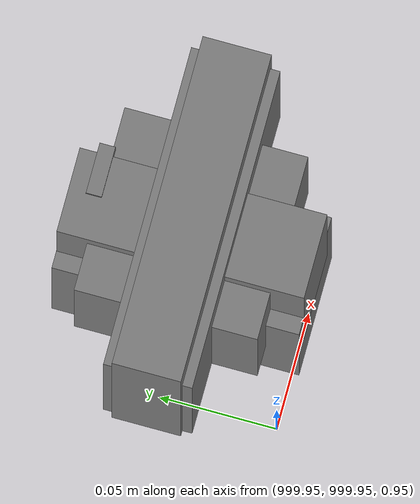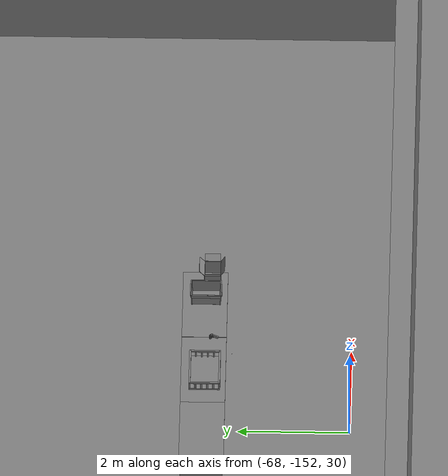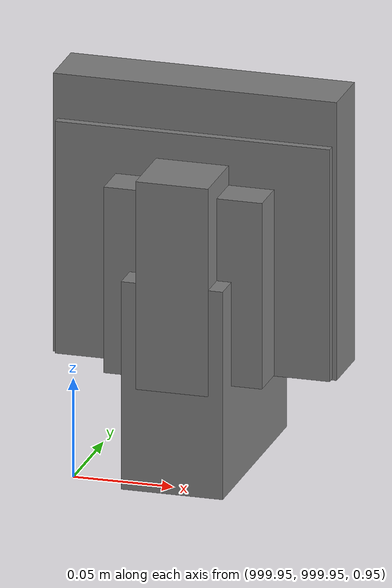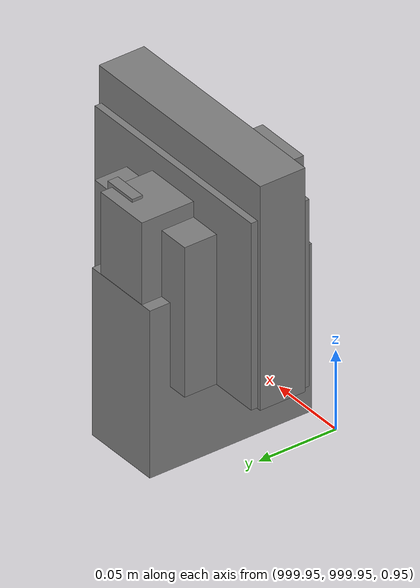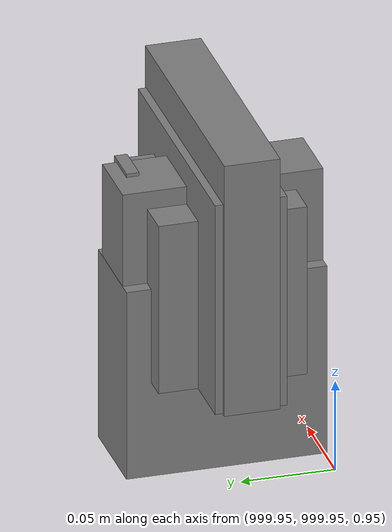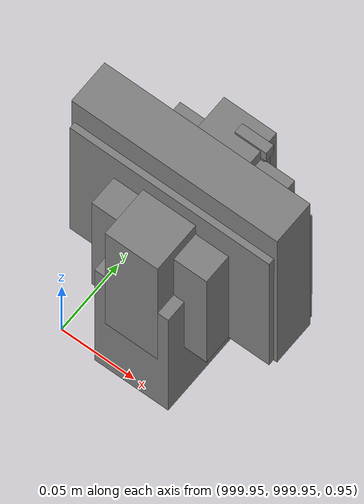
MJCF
<mujoco>
    <option gravity="0.000000000 0.000000000 -9.810000420" timestep="0.0049999999" integrator="implicitfast" density="1.225" viscosity="1.8000001e-05" noslip_iterations="10" iterations="100" sdf_iterations="50">
        <flag multiccd="disable"/>
    </option>
    <size memory="1000M"/>
    <compiler coordinate="local"/>
    <worldbody>
        <light cutoff="30" pos="0 1 1" dir="0 -1 -2"/>
        <light cutoff="30" pos="0 -1 1" dir="0 1 -2"/>
        <body pos="-64.866622925 -149.383972168 30.183746338" euler="89.999984741 89.999946594 0.000000000" name="openloong_gripper_2f85_fix_base_usda_bluebox_01">
            <geom contype="1" conaffinity="1" density="1000" type="box" material="" rgba="0.500000000 0.500000000 0.500000000 1.000000000" solimp="0.899999976 0.949999988 0.001000000" friction="1.000000000 0.005000000 0.000100000" solref="0.020000000 1.000000000" margin="0" condim="3" group="0" pos="0.276580811 0.187225342 0.000068665" quat="0.707106948 0.000077471 0.707106352 0.000077486" size="0.100000001 0.057999998 0.010000000" name="openloong_gripper_2f85_fix_base_usda_geom_0F1B6DC8_3AC1_4E5B_8AAC_50107FE5131D"/>
            <geom contype="1" conaffinity="1" density="1000" type="box" material="" rgba="0.500000000 0.500000000 0.500000000 1.000000000" solimp="0.899999976 0.949999988 0.001000000" friction="1.000000000 0.005000000 0.000100000" solref="0.020000000 1.000000000" margin="0" condim="3" group="0" pos="0.000000000 0.002883911 0.000000000" quat="0.999999881 0.000000000 0.000000000 0.000000000" size="0.254000008 0.003000000 0.172000006" name="openloong_gripper_2f85_fix_base_usda_geom_6780B717_DCAC_4721_B6C6_C7DD8B449B9B"/>
            <geom contype="1" conaffinity="1" density="1000" type="box" material="" rgba="0.500000000 0.500000000 0.500000000 1.000000000" solimp="0.899999976 0.949999988 0.001000000" friction="1.000000000 0.005000000 0.000100000" solref="0.020000000 1.000000000" margin="0" condim="3" group="0" pos="0.000000000 0.124874115 0.173484802" quat="0.999796331 0.020176515 -0.000000015 0.000000030" size="0.259999990 0.119999997 0.007000000" name="openloong_gripper_2f85_fix_base_usda_geom_E2D06F0A_83D1_4870_BD71_A2632364E8DB"/>
            <geom contype="1" conaffinity="1" density="1000" type="box" material="" rgba="0.500000000 0.500000000 0.500000000 1.000000000" solimp="0.899999976 0.949999988 0.001000000" friction="1.000000000 0.005000000 0.000100000" solref="0.020000000 1.000000000" margin="0" condim="3" group="0" pos="0.000000000 0.124874115 -0.173469543" quat="0.999796331 -0.020176545 -0.000000015 0.000000000" size="0.259999990 0.119999997 0.007000000" name="openloong_gripper_2f85_fix_base_usda_geom_4FD9E2EE_BBF5_4BB7_9EAE_3D326F1F7125"/>
            <geom contype="1" conaffinity="1" density="1000" type="box" material="" rgba="0.500000000 0.500000000 0.500000000 1.000000000" solimp="0.899999976 0.949999988 0.001000000" friction="1.000000000 0.005000000 0.000100000" solref="0.020000000 1.000000000" margin="0" condim="3" group="0" pos="0.000000000 0.214008331 0.188980103" quat="0.999912977 0.013176724 0.000000015 0.000000000" size="0.259999990 0.029999999 0.012500000" name="openloong_gripper_2f85_fix_base_usda_geom_9AFCADC2_EEBA_4918_A270_4BA211978459"/>
            <geom contype="1" conaffinity="1" density="1000" type="box" material="" rgba="0.500000000 0.500000000 0.500000000 1.000000000" solimp="0.899999976 0.949999988 0.001000000" friction="1.000000000 0.005000000 0.000100000" solref="0.020000000 1.000000000" margin="0" condim="3" group="0" pos="-0.258361816 0.125289917 0.001876831" quat="0.702796936 -0.020792112 0.710783124 0.020769298" size="0.189999998 0.119999997 0.009000000" name="openloong_gripper_2f85_fix_base_usda_geom_216B43D8_A7F0_493C_B185_04D58ED407D9"/>
            <geom contype="1" conaffinity="1" density="1000" type="box" material="" rgba="0.500000000 0.500000000 0.500000000 1.000000000" solimp="0.899999976 0.949999988 0.001000000" friction="1.000000000 0.005000000 0.000100000" solref="0.020000000 1.000000000" margin="0" condim="3" group="0" pos="0.000000000 0.214008331 -0.188980103" quat="0.999912977 -0.013176769 0.000000030 0.000000015" size="0.259999990 0.029999999 0.012500000" name="openloong_gripper_2f85_fix_base_usda_geom_93F78F68_1471_4E87_933A_0F025D2EAA96"/>
            <geom contype="1" conaffinity="1" density="1000" type="box" material="" rgba="0.500000000 0.500000000 0.500000000 1.000000000" solimp="0.899999976 0.949999988 0.001000000" friction="1.000000000 0.005000000 0.000100000" solref="0.020000000 1.000000000" margin="0" condim="3" group="0" pos="-0.276611328 0.187225342 0.000068665" quat="0.707106650 0.000077441 0.707106709 0.000077456" size="0.100000001 0.057999998 0.010000000" name="openloong_gripper_2f85_fix_base_usda_geom_994803A1_C3C4_4C47_8F08_2E4532EAFD53"/>
            <geom contype="1" conaffinity="1" density="1000" type="box" material="" rgba="0.500000000 0.500000000 0.500000000 1.000000000" solimp="0.899999976 0.949999988 0.001000000" friction="1.000000000 0.005000000 0.000100000" solref="0.020000000 1.000000000" margin="0" condim="3" group="0" pos="0.258331299 0.125289917 0.001876831" quat="0.702851415 0.018856421 0.710823774 -0.019329369" size="0.189999998 0.119999997 0.009000000" name="openloong_gripper_2f85_fix_base_usda_geom_85334F74_8C59_43D9_9346_7E53D9946CAC"/>
            <freejoint name="openloong_gripper_2f85_fix_base_usda_bluebox_01_joint"/>
            <site size="0.005000000 0.005000000 0.005000000" rgba="0.500000000 0.500000000 0.500000000 1.000000000" pos="0.000000000 0.000000000 0.000000000" quat="0.999961913 0.008726534 0.000000000 0.000000000" group="0" type="sphere" name="openloong_gripper_2f85_fix_base_usda_bluebox_01site"/>
        </body>
        <body pos="-64.496299744 -149.491867065 30.235729218" euler="0.000000000 0.000000000 89.999946594" name="openloong_gripper_2f85_fix_base_usda_cardboardbox_01">
            <geom contype="1" conaffinity="1" density="1000" type="box" material="" rgba="0.500000000 0.500000000 0.500000000 1.000000000" solimp="0.899999976 0.949999988 0.001000000" friction="1.000000000 0.005000000 0.000100000" solref="0.020000000 1.000000000" margin="0" condim="3" group="0" pos="-0.003166199 -0.004086494 0.005052090" quat="1.000000000 0.000000000 0.000000000 0.000000000" size="0.142499998 0.177500010 0.005000000" name="openloong_gripper_2f85_fix_base_usda_geom_271B6DEB_7E03_4B33_98F5_0F5E11EB32ED"/>
            <geom contype="1" conaffinity="1" density="1000" type="box" material="" rgba="0.500000000 0.500000000 0.500000000 1.000000000" solimp="0.899999976 0.949999988 0.001000000" friction="1.000000000 0.005000000 0.000100000" solref="0.020000000 1.000000000" margin="0" condim="3" group="0" pos="-0.003166199 0.170316696 0.150570869" quat="1.000000000 0.000000000 0.000000000 0.000000000" size="0.142499998 0.005000000 0.149999991" name="openloong_gripper_2f85_fix_base_usda_geom_BB20C261_3515_4029_A0D4_765D3B267D86"/>
            <geom contype="1" conaffinity="1" density="1000" type="box" material="" rgba="0.500000000 0.500000000 0.500000000 1.000000000" solimp="0.899999976 0.949999988 0.001000000" friction="1.000000000 0.005000000 0.000100000" solref="0.020000000 1.000000000" margin="0" condim="3" group="0" pos="-0.147399902 -0.005307198 0.150570869" quat="1.000000000 0.000000000 0.000000000 0.000000000" size="0.005000000 0.177500010 0.149999991" name="openloong_gripper_2f85_fix_base_usda_geom_20FC21AE_03A3_4F5E_9FD1_D04878C4B6CB"/>
            <geom contype="1" conaffinity="1" density="1000" type="box" material="" rgba="0.500000000 0.500000000 0.500000000 1.000000000" solimp="0.899999976 0.949999988 0.001000000" friction="1.000000000 0.005000000 0.000100000" solref="0.020000000 1.000000000" margin="0" condim="3" group="0" pos="0.140275955 -0.005307198 0.150570869" quat="1.000000000 0.000000000 0.000000000 0.000000000" size="0.005000000 0.177500010 0.149999991" name="openloong_gripper_2f85_fix_base_usda_geom_E5144BFA_2C21_4352_980A_3D9393FDAB89"/>
            <geom contype="1" conaffinity="1" density="1000" type="box" material="" rgba="0.500000000 0.500000000 0.500000000 1.000000000" solimp="0.899999976 0.949999988 0.001000000" friction="1.000000000 0.005000000 0.000100000" solref="0.020000000 1.000000000" margin="0" condim="3" group="0" pos="-0.003166199 -0.181550980 0.150570869" quat="1.000000000 0.000000000 0.000000000 0.000000000" size="0.142499998 0.005000000 0.149999991" name="openloong_gripper_2f85_fix_base_usda_geom_FB3970B3_6AA2_408A_85BB_07EDEEF8516A"/>
            <freejoint name="openloong_gripper_2f85_fix_base_usda_cardboardbox_01_joint"/>
            <site size="0.005000000 0.005000000 0.005000000" rgba="0.500000000 0.500000000 0.500000000 1.000000000" pos="0.000000000 0.000000000 0.000000000" quat="0.999961913 0.008726535 0.000000000 0.000000000" group="0" type="sphere" name="openloong_gripper_2f85_fix_base_usda_site_30133C3B_DF0A_4CD8_A968_77A763F0160C"/>
            <body pos="0.139160156 -0.004048347 0.301930904" euler="-179.999954224 49.383502960 179.999954224" name="openloong_gripper_2f85_fix_base_usda_A1_006">
                <geom contype="1" conaffinity="1" density="1000" type="box" material="" rgba="0.500000000 0.500000000 0.500000000 1.000000000" solimp="0.899999976 0.949999988 0.001000000" friction="1.000000000 0.005000000 0.000100000" solref="0.020000000 1.000000000" margin="0" condim="3" group="0" pos="-0.071587563 0.000009537 0.001745224" quat="0.999999881 0.000000000 0.000000000 0.000000000" size="0.071249999 0.179999992 0.002500000" name="openloong_gripper_2f85_fix_base_usda_geom_3C7C131A_7D9B_4268_A98D_960DA53AB3EB"/>
                <joint armature="0" stiffness="0.07" damping="0.0099999998" axis="0.000000 1.000000 0.000000" type="hinge" name="openloong_gripper_2f85_fix_base_usda_A1_006"/>
            </body>
            <body pos="-0.145902634 -0.004086494 0.301938057" euler="-180.000000000 -60.000011444 -180.000000000" name="openloong_gripper_2f85_fix_base_usda_A2_006">
                <geom contype="1" conaffinity="1" density="1000" type="box" material="" rgba="0.500000000 0.500000000 0.500000000 1.000000000" solimp="0.899999976 0.949999988 0.001000000" friction="1.000000000 0.005000000 0.000100000" solref="0.020000000 1.000000000" margin="0" condim="3" group="0" pos="0.071268082 0.000009537 0.002717972" quat="0.000002921 0.000000000 -0.000000030 0.999999881" size="0.071249999 0.179999992 0.002500000" name="openloong_gripper_2f85_fix_base_usda_geom_89D60E5B_3C14_4A74_9A90_0828B6D2612D"/>
                <joint armature="0" stiffness="0.07" damping="0.0099999998" axis="0.000000 1.000000 0.000000" type="hinge" name="openloong_gripper_2f85_fix_base_usda_A2_006"/>
            </body>
            <body pos="-0.003385544 0.175991058 0.301930904" euler="-125.858116150 -0.000004561 0.000002331" name="openloong_gripper_2f85_fix_base_usda_B2_006">
                <geom contype="1" conaffinity="1" density="1000" type="box" material="" rgba="0.500000000 0.500000000 0.500000000 1.000000000" solimp="0.899999976 0.949999988 0.001000000" friction="1.000000000 0.005000000 0.000100000" solref="0.020000000 1.000000000" margin="0" condim="3" group="0" pos="0.000009537 -0.070939064 -0.002470016" quat="0.999614120 0.027776197 -0.000000015 0.000000030" size="0.137500003 0.064999998 0.005000000" name="openloong_gripper_2f85_fix_base_usda_geom_E8E2C942_424A_4EC9_99FF_F54CB3EFB05F"/>
                <joint armature="0" stiffness="0.07" damping="0.0099999998" axis="1.000000 0.000000 0.000000" type="hinge" name="openloong_gripper_2f85_fix_base_usda_B2_006"/>
            </body>
            <body pos="-0.003385544 -0.184140205 0.301938057" euler="147.805557251 0.000000000 0.000000000" name="openloong_gripper_2f85_fix_base_usda_B1_006">
                <geom contype="1" conaffinity="1" density="1000" type="box" material="" rgba="0.500000000 0.500000000 0.500000000 1.000000000" solimp="0.899999976 0.949999988 0.001000000" friction="1.000000000 0.005000000 0.000100000" solref="0.020000000 1.000000000" margin="0" condim="3" group="0" pos="-0.000028610 0.070202351 -0.002703667" quat="0.999614179 -0.027776167 0.000000000 0.000000000" size="0.137500003 0.064999998 0.005000000" name="openloong_gripper_2f85_fix_base_usda_geom_C2DA11D6_A4EC_4F7D_AB0E_29D3CE9D0CF6"/>
                <joint armature="0" stiffness="0.07" damping="0.0099999998" axis="1.000000 0.000000 0.000000" type="hinge" name="openloong_gripper_2f85_fix_base_usda_B1_006"/>
            </body>
        </body>
        <body pos="-65.882858276 -149.481979370 30.229999542" euler="-64.487716675 0.000000000 0.000000000" name="openloong_gripper_2f85_fix_base_usda_Barcode">
            <geom contype="1" conaffinity="1" density="1000" type="box" material="" rgba="0.500000000 0.500000000 0.500000000 1.000000000" solimp="0.899999976 0.949999988 0.001000000" friction="1.000000000 0.005000000 0.000100000" solref="0.020000000 1.000000000" margin="0" condim="3" group="0" pos="0.000000000 0.013038635 0.001419067" quat="0.000000000 0.000000000 0.000000000 1.000000119" size="0.034000002 0.010000000 0.017999999" name="openloong_gripper_2f85_fix_base_usda_geom_56D17534_B6B3_43D2_898B_2E09D40ECC7D"/>
            <geom contype="1" conaffinity="1" density="1000" type="box" material="" rgba="0.500000000 0.500000000 0.500000000 1.000000000" solimp="0.899999976 0.949999988 0.001000000" friction="1.000000000 0.005000000 0.000100000" solref="0.020000000 1.000000000" margin="0" condim="3" group="0" pos="0.000000000 -0.035301208 -0.007095337" quat="0.000000000 0.000000000 -0.043619365 0.999048233" size="0.028999999 0.010000000 0.020000000" name="openloong_gripper_2f85_fix_base_usda_geom_3E5ED2E2_ACA3_40EB_A74A_B39263EC1C12"/>
            <geom contype="1" conaffinity="1" density="1000" type="box" material="" rgba="0.500000000 0.500000000 0.500000000 1.000000000" solimp="0.899999976 0.949999988 0.001000000" friction="1.000000000 0.005000000 0.000100000" solref="0.020000000 1.000000000" margin="0" condim="3" group="0" pos="0.000000000 -0.043411255 -0.011749268" quat="0.922262907 0.386563420 0.000000000 0.000000000" size="0.026000001 0.010000000 0.020000000" name="openloong_gripper_2f85_fix_base_usda_geom_2EEEA938_26C6_4401_A774_B50EF23AD596"/>
            <geom contype="1" conaffinity="1" density="1000" type="box" material="" rgba="0.500000000 0.500000000 0.500000000 1.000000000" solimp="0.899999976 0.949999988 0.001000000" friction="1.000000000 0.005000000 0.000100000" solref="0.020000000 1.000000000" margin="0" condim="3" group="0" pos="0.000000000 -0.016967773 -0.031860352" quat="0.000000000 0.000000000 0.000000000 1.000000119" size="0.008000000 0.010000000 0.013000000" name="openloong_gripper_2f85_fix_base_usda_geom_5A664FF4_9C87_462F_9E10_8AA7F712E8F1"/>
            <geom contype="1" conaffinity="1" density="1000" type="box" material="" rgba="0.500000000 0.500000000 0.500000000 1.000000000" solimp="0.899999976 0.949999988 0.001000000" friction="1.000000000 0.005000000 0.000100000" solref="0.020000000 1.000000000" margin="0" condim="3" group="0" pos="0.000000000 -0.001869202 0.000312805" quat="0.953716993 0.300705761 0.000000000 0.000000000" size="0.032000002 0.010000000 0.018999999" name="openloong_gripper_2f85_fix_base_usda_geom_5F66F734_0F44_4AFF_932A_057CDB7C6D45"/>
            <geom contype="1" conaffinity="1" density="1000" type="box" material="" rgba="0.500000000 0.500000000 0.500000000 1.000000000" solimp="0.899999976 0.949999988 0.001000000" friction="1.000000000 0.005000000 0.000100000" solref="0.020000000 1.000000000" margin="0" condim="3" group="0" pos="0.000000000 -0.019531250 -0.003173828" quat="0.953716993 0.300705761 0.000000000 0.000000000" size="0.030999999 0.010000000 0.020000000" name="openloong_gripper_2f85_fix_base_usda_geom_4BCB02F6_0873_4A09_8058_C66599D89A54"/>
            <geom contype="1" conaffinity="1" density="1000" type="box" material="" rgba="0.500000000 0.500000000 0.500000000 1.000000000" solimp="0.899999976 0.949999988 0.001000000" friction="1.000000000 0.005000000 0.000100000" solref="0.020000000 1.000000000" margin="0" condim="3" group="0" pos="0.000000000 -0.035301208 -0.007095337" quat="0.953716993 0.300705761 0.000000000 0.000000000" size="0.028999999 0.010000000 0.020000000" name="openloong_gripper_2f85_fix_base_usda_geom_8B7FAF1F_895C_4F3C_93D5_AA077A2344B1"/>
            <geom contype="1" conaffinity="1" density="1000" type="box" material="" rgba="0.500000000 0.500000000 0.500000000 1.000000000" solimp="0.899999976 0.949999988 0.001000000" friction="1.000000000 0.005000000 0.000100000" solref="0.020000000 1.000000000" margin="0" condim="3" group="0" pos="0.000000000 -0.042617798 -0.071121216" quat="0.000000000 0.000000000 0.000000000 1.000000119" size="0.013000000 0.021000000 0.059999999" name="openloong_gripper_2f85_fix_base_usda_geom_A3F4027C_43C3_42A0_A09E_8DB0A470EDEF"/>
            <freejoint name="openloong_gripper_2f85_fix_base_usda_Barcode_joint"/>
            <site size="0.005000000 0.005000000 0.005000000" rgba="0.500000000 0.500000000 0.500000000 1.000000000" pos="0.000000000 0.000000000 0.000000000" quat="1.000000000 0.000000000 0.000000000 0.000000000" group="0" type="sphere" name="openloong_gripper_2f85_fix_base_usda_Barcode_site"/>
        </body>
        <body pos="-66.745018005 -149.392349243 30.184000015" euler="0.000000000 0.000000000 89.999946594" name="[22331858217657]_Basket_01">
            <geom contype="1" conaffinity="1" density="1000" type="box" material="" rgba="0.500000000 0.500000000 0.500000000 1.000000000" solimp="0.899999976 0.949999988 0.001000000" friction="1.000000000 0.005000000 0.000100000" solref="0.020000000 1.000000000" margin="0" condim="3" group="0" pos="-0.052425385 0.389207840 0.089787483" quat="0.707107008 0.000000000 0.000000000 0.707106411" size="0.014249999 0.014249999 0.059999999" name="[22331858217657]_geom_9CD26791_A482_441D_8735_095DDAABF195"/>
            <geom contype="1" conaffinity="1" density="1000" type="box" material="" rgba="0.500000000 0.500000000 0.500000000 1.000000000" solimp="0.899999976 0.949999988 0.001000000" friction="1.000000000 0.005000000 0.000100000" solref="0.020000000 1.000000000" margin="0" condim="3" group="0" pos="0.264015198 -0.133043289 0.089787483" quat="0.707107008 0.000000000 0.000000000 0.707106411" size="0.014249999 0.014249999 0.059999999" name="[22331858217657]_geom_61457355_6361_4EC4_B932_6CCFD250CE13"/>
            <geom contype="1" conaffinity="1" density="1000" type="box" material="" rgba="0.500000000 0.500000000 0.500000000 1.000000000" solimp="0.899999976 0.949999988 0.001000000" friction="1.000000000 0.005000000 0.000100000" solref="0.020000000 1.000000000" margin="0" condim="3" group="0" pos="-0.264015198 -0.265548706 0.089793205" quat="0.707107008 0.000000000 0.000000000 0.707106411" size="0.014249999 0.014249999 0.059999999" name="[22331858217657]_geom_D8305FAF_626D_4DFD_BF48_0972103AD2C4"/>
            <geom contype="1" conaffinity="1" density="1000" type="box" material="" rgba="0.500000000 0.500000000 0.500000000 1.000000000" solimp="0.899999976 0.949999988 0.001000000" friction="1.000000000 0.005000000 0.000100000" solref="0.020000000 1.000000000" margin="0" condim="3" group="0" pos="-0.160263062 -0.389322281 0.089793205" quat="0.707107008 0.000000000 0.000000000 0.707106411" size="0.014249999 0.014249999 0.059999999" name="[22331858217657]_geom_5F478C2F_B86C_4FB4_95C6_24B49103440B"/>
            <geom contype="1" conaffinity="1" density="1000" type="box" material="" rgba="0.500000000 0.500000000 0.500000000 1.000000000" solimp="0.899999976 0.949999988 0.001000000" friction="1.000000000 0.005000000 0.000100000" solref="0.020000000 1.000000000" margin="0" condim="3" group="0" pos="0.162265778 -0.389322281 0.089787483" quat="0.707107008 0.000000000 0.000000000 0.707106411" size="0.014249999 0.014249999 0.059999999" name="[22331858217657]_geom_652EEFCC_F9C7_4678_B13E_854CCC39D2DD"/>
            <geom contype="1" conaffinity="1" density="1000" type="box" material="" rgba="0.500000000 0.500000000 0.500000000 1.000000000" solimp="0.899999976 0.949999988 0.001000000" friction="1.000000000 0.005000000 0.000100000" solref="0.020000000 1.000000000" margin="0" condim="3" group="0" pos="0.264015198 0.389207840 0.089787483" quat="0.707107008 0.000000000 0.000000000 0.707106411" size="0.014249999 0.014249999 0.059999999" name="[22331858217657]_geom_AE392958_E800_4F23_9DFE_2576D23E5DB1"/>
            <geom contype="1" conaffinity="1" density="1000" type="box" material="" rgba="0.500000000 0.500000000 0.500000000 1.000000000" solimp="0.899999976 0.949999988 0.001000000" friction="1.000000000 0.005000000 0.000100000" solref="0.020000000 1.000000000" margin="0" condim="3" group="0" pos="-0.264015198 -0.133043289 0.089793205" quat="0.707107008 0.000000000 0.000000000 0.707106411" size="0.014249999 0.014249999 0.059999999" name="[22331858217657]_geom_89BA8D7E_05EC_46EA_86BD_6B917B4BA6B2"/>
            <geom contype="1" conaffinity="1" density="1000" type="box" material="" rgba="0.500000000 0.500000000 0.500000000 1.000000000" solimp="0.899999976 0.949999988 0.001000000" friction="1.000000000 0.005000000 0.000100000" solref="0.020000000 1.000000000" margin="0" condim="3" group="0" pos="-0.264026642 0.269256592 0.089793205" quat="0.707107008 0.000000000 0.000000000 0.707106411" size="0.014249999 0.014249999 0.059999999" name="[22331858217657]_geom_F39E5817_E2D0_422F_AD03_95DF5CF4083B"/>
            <geom contype="1" conaffinity="1" density="1000" type="box" material="" rgba="0.500000000 0.500000000 0.500000000 1.000000000" solimp="0.899999976 0.949999988 0.001000000" friction="1.000000000 0.005000000 0.000100000" solref="0.020000000 1.000000000" margin="0" condim="3" group="0" pos="0.054462433 0.389207840 0.089787483" quat="0.707107008 0.000000000 0.000000000 0.707106411" size="0.014249999 0.014249999 0.059999999" name="[22331858217657]_geom_B304DA9C_2B1F_4EA1_8175_7170FA1D88FF"/>
            <geom contype="1" conaffinity="1" density="1000" type="box" material="" rgba="0.500000000 0.500000000 0.500000000 1.000000000" solimp="0.899999976 0.949999988 0.001000000" friction="1.000000000 0.005000000 0.000100000" solref="0.020000000 1.000000000" margin="0" condim="3" group="0" pos="0.054462433 -0.389322281 0.089787483" quat="0.707107008 0.000000000 0.000000000 0.707106411" size="0.014249999 0.014249999 0.059999999" name="[22331858217657]_geom_F9498170_BB1B_40AA_ADAF_750DA07B47B7"/>
            <geom contype="1" conaffinity="1" density="1000" type="box" material="" rgba="0.500000000 0.500000000 0.500000000 1.000000000" solimp="0.899999976 0.949999988 0.001000000" friction="1.000000000 0.005000000 0.000100000" solref="0.020000000 1.000000000" margin="0" condim="3" group="0" pos="0.264015198 0.269256592 0.089793205" quat="0.707107008 0.000000000 0.000000000 0.707106411" size="0.014249999 0.014249999 0.059999999" name="[22331858217657]_geom_6A80B092_45B1_415B_9005_7453C278B78C"/>
            <geom contype="1" conaffinity="1" density="1000" type="box" material="" rgba="0.500000000 0.500000000 0.500000000 1.000000000" solimp="0.899999976 0.949999988 0.001000000" friction="1.000000000 0.005000000 0.000100000" solref="0.020000000 1.000000000" margin="0" condim="3" group="0" pos="0.264015198 -0.389322281 0.089787483" quat="0.707107008 0.000000000 0.000000000 0.707106411" size="0.014249999 0.014249999 0.059999999" name="[22331858217657]_geom_C45B3679_7B5C_4F4A_9AA8_53E4B915E6AE"/>
            <geom contype="1" conaffinity="1" density="1000" type="box" material="" rgba="0.500000000 0.500000000 0.500000000 1.000000000" solimp="0.899999976 0.949999988 0.001000000" friction="1.000000000 0.005000000 0.000100000" solref="0.020000000 1.000000000" margin="0" condim="3" group="0" pos="0.000000000 0.000000000 0.015998840" quat="0.707107008 0.000000000 0.000000000 0.707106411" size="0.403499991 0.279000014 0.015750000" name="[22331858217657]_geom_9AD81F2D_2C3F_4D67_8624_4A57AFD6BEEE"/>
            <geom contype="1" conaffinity="1" density="1000" type="box" material="" rgba="0.500000000 0.500000000 0.500000000 1.000000000" solimp="0.899999976 0.949999988 0.001000000" friction="1.000000000 0.005000000 0.000100000" solref="0.020000000 1.000000000" margin="0" condim="3" group="0" pos="0.000000000 -0.389476776 0.163619041" quat="0.707107008 0.000000000 0.000000000 0.707106411" size="0.015000000 0.277500004 0.015750000" name="[22331858217657]_geom_BA79B500_C035_4D25_9D0A_9E90662E4513"/>
            <geom contype="1" conaffinity="1" density="1000" type="box" material="" rgba="0.500000000 0.500000000 0.500000000 1.000000000" solimp="0.899999976 0.949999988 0.001000000" friction="1.000000000 0.005000000 0.000100000" solref="0.020000000 1.000000000" margin="0" condim="3" group="0" pos="0.162265778 0.389207840 0.089787483" quat="0.707107008 0.000000000 0.000000000 0.707106411" size="0.014249999 0.014249999 0.059999999" name="[22331858217657]_geom_6D2E6971_C545_468C_8080_6A68AA4356DE"/>
            <geom contype="1" conaffinity="1" density="1000" type="box" material="" rgba="0.500000000 0.500000000 0.500000000 1.000000000" solimp="0.899999976 0.949999988 0.001000000" friction="1.000000000 0.005000000 0.000100000" solref="0.020000000 1.000000000" margin="0" condim="3" group="0" pos="0.000000000 0.389471054 0.163619041" quat="0.707107008 0.000000000 0.000000000 0.707106411" size="0.015000000 0.277500004 0.015750000" name="[22331858217657]_geom_FEBA4B8E_5EA9_495C_A2D0_BEF023C863AA"/>
            <geom contype="1" conaffinity="1" density="1000" type="box" material="" rgba="0.500000000 0.500000000 0.500000000 1.000000000" solimp="0.899999976 0.949999988 0.001000000" friction="1.000000000 0.005000000 0.000100000" solref="0.020000000 1.000000000" margin="0" condim="3" group="0" pos="-0.263511658 0.000000000 0.163619041" quat="0.707107008 0.000000000 0.000000000 0.707106411" size="0.403499991 0.015000000 0.015750000" name="[22331858217657]_geom_A9718723_5A17_4735_A166_51A7FBDF2779"/>
            <geom contype="1" conaffinity="1" density="1000" type="box" material="" rgba="0.500000000 0.500000000 0.500000000 1.000000000" solimp="0.899999976 0.949999988 0.001000000" friction="1.000000000 0.005000000 0.000100000" solref="0.020000000 1.000000000" margin="0" condim="3" group="0" pos="-0.264015198 0.141334534 0.089793205" quat="0.707107008 0.000000000 0.000000000 0.707106411" size="0.014249999 0.014249999 0.059999999" name="[22331858217657]_geom_9E0FFFC4_4505_40B6_95D5_89DF0FC1633E"/>
            <geom contype="1" conaffinity="1" density="1000" type="box" material="" rgba="0.500000000 0.500000000 0.500000000 1.000000000" solimp="0.899999976 0.949999988 0.001000000" friction="1.000000000 0.005000000 0.000100000" solref="0.020000000 1.000000000" margin="0" condim="3" group="0" pos="0.264015198 -0.265548706 0.089787483" quat="0.707107008 0.000000000 0.000000000 0.707106411" size="0.014249999 0.014249999 0.059999999" name="[22331858217657]_geom_BE30B6E0_6CAF_43EC_8A93_0F6222C24859"/>
            <geom contype="1" conaffinity="1" density="1000" type="box" material="" rgba="0.500000000 0.500000000 0.500000000 1.000000000" solimp="0.899999976 0.949999988 0.001000000" friction="1.000000000 0.005000000 0.000100000" solref="0.020000000 1.000000000" margin="0" condim="3" group="0" pos="-0.160263062 0.389207840 0.089787483" quat="0.707107008 0.000000000 0.000000000 0.707106411" size="0.014249999 0.014249999 0.059999999" name="[22331858217657]_geom_A9BBF658_CA6B_46C0_ABAB_68FABD95914C"/>
            <geom contype="1" conaffinity="1" density="1000" type="box" material="" rgba="0.500000000 0.500000000 0.500000000 1.000000000" solimp="0.899999976 0.949999988 0.001000000" friction="1.000000000 0.005000000 0.000100000" solref="0.020000000 1.000000000" margin="0" condim="3" group="0" pos="-0.052425385 -0.389322281 0.089787483" quat="0.707107008 0.000000000 0.000000000 0.707106411" size="0.014249999 0.014249999 0.059999999" name="[22331858217657]_geom_42C0DE53_3425_4B14_9683_8F6E48E914EB"/>
            <geom contype="1" conaffinity="1" density="1000" type="box" material="" rgba="0.500000000 0.500000000 0.500000000 1.000000000" solimp="0.899999976 0.949999988 0.001000000" friction="1.000000000 0.005000000 0.000100000" solref="0.020000000 1.000000000" margin="0" condim="3" group="0" pos="-0.264026642 -0.389322281 0.089793205" quat="0.707107008 0.000000000 0.000000000 0.707106411" size="0.014249999 0.014249999 0.059999999" name="[22331858217657]_geom_D670981D_9E08_4C00_BE43_286265159870"/>
            <geom contype="1" conaffinity="1" density="1000" type="box" material="" rgba="0.500000000 0.500000000 0.500000000 1.000000000" solimp="0.899999976 0.949999988 0.001000000" friction="1.000000000 0.005000000 0.000100000" solref="0.020000000 1.000000000" margin="0" condim="3" group="0" pos="0.264015198 0.141334534 0.089787483" quat="0.707107008 0.000000000 0.000000000 0.707106411" size="0.014249999 0.014249999 0.059999999" name="[22331858217657]_geom_89B5C4DE_7F3D_4016_BC63_7379AF49898C"/>
            <geom contype="1" conaffinity="1" density="1000" type="box" material="" rgba="0.500000000 0.500000000 0.500000000 1.000000000" solimp="0.899999976 0.949999988 0.001000000" friction="1.000000000 0.005000000 0.000100000" solref="0.020000000 1.000000000" margin="0" condim="3" group="0" pos="-0.264015198 0.389207840 0.089793205" quat="0.707107008 0.000000000 0.000000000 0.707106411" size="0.014249999 0.014249999 0.059999999" name="[22331858217657]_geom_C7DBBFF9_DE91_46D8_BCD6_412D84EF85DE"/>
            <geom contype="1" conaffinity="1" density="1000" type="box" material="" rgba="0.500000000 0.500000000 0.500000000 1.000000000" solimp="0.899999976 0.949999988 0.001000000" friction="1.000000000 0.005000000 0.000100000" solref="0.020000000 1.000000000" margin="0" condim="3" group="0" pos="0.264015198 0.004480362 0.089787483" quat="0.707107008 0.000000000 0.000000000 0.707106411" size="0.014249999 0.014249999 0.059999999" name="[22331858217657]_geom_3578D46B_3DE7_4771_ACDF_F912E69B8406"/>
            <geom contype="1" conaffinity="1" density="1000" type="box" material="" rgba="0.500000000 0.500000000 0.500000000 1.000000000" solimp="0.899999976 0.949999988 0.001000000" friction="1.000000000 0.005000000 0.000100000" solref="0.020000000 1.000000000" margin="0" condim="3" group="0" pos="0.263694763 -0.000011444 0.163619041" quat="0.707107008 0.000000000 0.000000000 0.707106411" size="0.403499991 0.015000000 0.015750000" name="[22331858217657]_geom_4141A740_743D_4DC8_B4D5_C845B988A02A"/>
            <geom contype="1" conaffinity="1" density="1000" type="box" material="" rgba="0.500000000 0.500000000 0.500000000 1.000000000" solimp="0.899999976 0.949999988 0.001000000" friction="1.000000000 0.005000000 0.000100000" solref="0.020000000 1.000000000" margin="0" condim="3" group="0" pos="-0.264015198 0.004480362 0.089793205" quat="0.707107008 0.000000000 0.000000000 0.707106411" size="0.014249999 0.014249999 0.059999999" name="[22331858217657]_geom_7F925BB0_7B06_4FBB_A9FF_8440C7FA362B"/>
            <freejoint name="[22331858217657]_joint_FDB1F74E_F934_46BB_9E12_0707A9F72FF6"/>
        </body>
        <body pos="0.000000000 0.000000000 0.000000000" euler="0.000000000 0.000000000 0.000000000" name="Static Objects_Static Objects">
            <geom contype="1" conaffinity="1" density="1000" type="box" material="" rgba="0.500000000 0.500000000 0.500000000 1.000000000" solimp="0.899999976 0.949999988 0.001000000" friction="1.000000000 0.005000000 0.000100000" solref="0.020000000 1.000000000" margin="0" condim="3" group="0" pos="-67.544113159 -149.365814209 29.727830887" quat="0.500000417 0.499999970 0.499999553 0.499999970" size="0.381000012 0.319999993 0.041000001" name="Static Objects_geom_9D4A64A8_EBFE_4ED2_AFBF_E3AF8B0007C1"/>
            <geom contype="1" conaffinity="1" density="1000" type="box" material="" rgba="0.500000000 0.500000000 0.500000000 1.000000000" solimp="0.899999976 0.949999988 0.001000000" friction="1.000000000 0.005000000 0.000100000" solref="0.020000000 1.000000000" margin="0" condim="3" group="0" pos="-68.239501953 -149.365814209 30.086868286" quat="0.500000417 0.499999970 0.499999553 0.499999970" size="0.370999992 0.039500002 0.745000005" name="Static Objects_geom_A613637E_8E47_43FE_9834_D72DEFFAB302"/>
            <geom contype="1" conaffinity="1" density="1000" type="box" material="" rgba="0.500000000 0.500000000 0.500000000 1.000000000" solimp="0.899999976 0.949999988 0.001000000" friction="1.000000000 0.005000000 0.000100000" solref="0.020000000 1.000000000" margin="0" condim="3" group="0" pos="-68.239501953 -149.365814209 30.147235870" quat="0.500000417 0.499999970 0.499999553 0.499999970" size="0.400000006 0.022000000 0.800000012" name="Static Objects_geom_B0EA8028_86DB_4142_BA54_6D204B720DA1"/>
            <geom contype="1" conaffinity="1" density="1000" type="box" material="" rgba="0.500000000 0.500000000 0.500000000 1.000000000" solimp="0.899999976 0.949999988 0.001000000" friction="1.000000000 0.005000000 0.000100000" solref="0.020000000 1.000000000" margin="0" condim="3" group="0" pos="-68.934890747 -149.365814209 29.727830887" quat="0.500000417 0.499999970 0.499999553 0.499999970" size="0.381000012 0.319999993 0.041000001" name="Static Objects_geom_4722C10D_962B_4FBA_88F1_E860DF90448A"/>
            <geom contype="1" conaffinity="1" density="1000" type="box" material="" rgba="0.500000000 0.500000000 0.500000000 1.000000000" solimp="0.899999976 0.949999988 0.001000000" friction="1.000000000 0.005000000 0.000100000" solref="0.020000000 1.000000000" margin="0" condim="3" group="0" pos="-68.239501953 -149.365814209 29.561563492" quat="0.500000417 0.499999970 0.499999553 0.499999970" size="0.020000000 0.022000000 0.660000026" name="Static Objects_geom_BC8BB2E6_5001_4720_A6E7_DCEF6B664626"/>
            <geom contype="1" conaffinity="1" density="1000" type="box" material="" rgba="0.500000000 0.500000000 0.500000000 1.000000000" solimp="0.899999976 0.949999988 0.001000000" friction="1.000000000 0.005000000 0.000100000" solref="0.020000000 1.000000000" margin="0" condim="3" group="0" pos="-65.945671082 -149.365814209 29.727830887" quat="0.500000417 0.499999970 0.499999553 0.499999970" size="0.381000012 0.319999993 0.041000001" name="Static Objects_geom_416B0602_110F_4568_8180_312D1AFEBA3A"/>
            <geom contype="1" conaffinity="1" density="1000" type="box" material="" rgba="0.500000000 0.500000000 0.500000000 1.000000000" solimp="0.899999976 0.949999988 0.001000000" friction="1.000000000 0.005000000 0.000100000" solref="0.020000000 1.000000000" margin="0" condim="3" group="0" pos="-66.641059875 -149.365814209 30.086868286" quat="0.500000417 0.499999970 0.499999553 0.499999970" size="0.370999992 0.039500002 0.745000005" name="Static Objects_geom_5F747033_8F92_498D_BB91_4CF461E0C7B4"/>
            <geom contype="1" conaffinity="1" density="1000" type="box" material="" rgba="0.500000000 0.500000000 0.500000000 1.000000000" solimp="0.899999976 0.949999988 0.001000000" friction="1.000000000 0.005000000 0.000100000" solref="0.020000000 1.000000000" margin="0" condim="3" group="0" pos="-66.641059875 -149.365814209 30.147235870" quat="0.500000417 0.499999970 0.499999553 0.499999970" size="0.400000006 0.022000000 0.800000012" name="Static Objects_geom_FE8F3304_C6F9_4A72_9C7C_44220896B745"/>
            <geom contype="1" conaffinity="1" density="1000" type="box" material="" rgba="0.500000000 0.500000000 0.500000000 1.000000000" solimp="0.899999976 0.949999988 0.001000000" friction="1.000000000 0.005000000 0.000100000" solref="0.020000000 1.000000000" margin="0" condim="3" group="0" pos="-67.336448669 -149.365814209 29.727830887" quat="0.500000417 0.499999970 0.499999553 0.499999970" size="0.381000012 0.319999993 0.041000001" name="Static Objects_geom_89642A7D_0D8F_47B7_8EC2_EC1C3C6BE72E"/>
            <geom contype="1" conaffinity="1" density="1000" type="box" material="" rgba="0.500000000 0.500000000 0.500000000 1.000000000" solimp="0.899999976 0.949999988 0.001000000" friction="1.000000000 0.005000000 0.000100000" solref="0.020000000 1.000000000" margin="0" condim="3" group="0" pos="-66.641059875 -149.365814209 29.561563492" quat="0.500000417 0.499999970 0.499999553 0.499999970" size="0.020000000 0.022000000 0.660000026" name="Static Objects_geom_957F4DC8_A66D_4155_818A_046F2AA6ACA4"/>
            <geom contype="1" conaffinity="1" density="1000" type="box" material="" rgba="0.500000000 0.500000000 0.500000000 1.000000000" solimp="0.899999976 0.949999988 0.001000000" friction="1.000000000 0.005000000 0.000100000" solref="0.020000000 1.000000000" margin="0" condim="3" group="0" pos="-64.338577271 -149.365814209 29.727830887" quat="0.500000417 0.499999970 0.499999553 0.499999970" size="0.381000012 0.319999993 0.041000001" name="Static Objects_geom_F006846A_4FE7_42E7_A60F_4317F12F21A0"/>
            <geom contype="1" conaffinity="1" density="1000" type="box" material="" rgba="0.500000000 0.500000000 0.500000000 1.000000000" solimp="0.899999976 0.949999988 0.001000000" friction="1.000000000 0.005000000 0.000100000" solref="0.020000000 1.000000000" margin="0" condim="3" group="0" pos="-65.033966064 -149.365814209 30.086868286" quat="0.500000417 0.499999970 0.499999553 0.499999970" size="0.370999992 0.039500002 0.745000005" name="Static Objects_geom_8215B345_BF19_4711_92DB_BE72399789A2"/>
            <geom contype="1" conaffinity="1" density="1000" type="box" material="" rgba="0.500000000 0.500000000 0.500000000 1.000000000" solimp="0.899999976 0.949999988 0.001000000" friction="1.000000000 0.005000000 0.000100000" solref="0.020000000 1.000000000" margin="0" condim="3" group="0" pos="-65.033966064 -149.365814209 30.147235870" quat="0.500000417 0.499999970 0.499999553 0.499999970" size="0.400000006 0.022000000 0.800000012" name="Static Objects_geom_A5B566B5_96D2_457E_9953_B2EA7820D343"/>
            <geom contype="1" conaffinity="1" density="1000" type="box" material="" rgba="0.500000000 0.500000000 0.500000000 1.000000000" solimp="0.899999976 0.949999988 0.001000000" friction="1.000000000 0.005000000 0.000100000" solref="0.020000000 1.000000000" margin="0" condim="3" group="0" pos="-65.729354858 -149.365814209 29.727830887" quat="0.500000417 0.499999970 0.499999553 0.499999970" size="0.381000012 0.319999993 0.041000001" name="Static Objects_geom_AE247380_4A33_4F3A_8F53_351CC5BC4640"/>
            <geom contype="1" conaffinity="1" density="1000" type="box" material="" rgba="0.500000000 0.500000000 0.500000000 1.000000000" solimp="0.899999976 0.949999988 0.001000000" friction="1.000000000 0.005000000 0.000100000" solref="0.020000000 1.000000000" margin="0" condim="3" group="0" pos="-65.033966064 -149.365814209 29.561563492" quat="0.500000417 0.499999970 0.499999553 0.499999970" size="0.020000000 0.022000000 0.660000026" name="Static Objects_geom_C8B98FC2_B5FA_480D_903D_28476780791D"/>
            <geom contype="1" conaffinity="1" density="1000" type="box" material="" rgba="0.500000000 0.500000000 0.500000000 1.000000000" solimp="0.899999976 0.949999988 0.001000000" friction="1.000000000 0.005000000 0.000100000" solref="0.020000000 1.000000000" margin="0" condim="3" group="0" pos="-61.754566193 -137.853729248 33.906845093" quat="0.707107067 0.000000000 0.000000000 0.707106471" size="0.759999990 0.759999990 4.500000000" name="Static Objects_geom_0B71013D_BCC4_4F5D_95B9_DFCDBE83F433"/>
            <geom contype="1" conaffinity="1" density="1000" type="box" material="" rgba="0.500000000 0.500000000 0.500000000 1.000000000" solimp="0.899999976 0.949999988 0.001000000" friction="1.000000000 0.005000000 0.000100000" solref="0.020000000 1.000000000" margin="0" condim="3" group="0" pos="-57.511135101 -144.927108765 31.707921982" quat="1.000000000 0.000000000 0.000000000 0.000000000" size="0.200000003 8.000000000 2.299999952" name="Static Objects_geom_E480AF9B_395B_4DA9_A348_2138D8AE8ACB"/>
            <geom contype="1" conaffinity="1" density="1000" type="box" material="" rgba="0.500000000 0.500000000 0.500000000 1.000000000" solimp="0.899999976 0.949999988 0.001000000" friction="1.000000000 0.005000000 0.000100000" solref="0.020000000 1.000000000" margin="0" condim="3" group="0" pos="-80.517646790 -157.574050903 31.688196182" quat="0.707107067 0.000000000 0.000000000 0.707106471" size="0.600000024 0.600000024 2.299999952" name="Static Objects_geom_E23998AE_3573_4349_90AB_46615EE747BF"/>
            <geom contype="1" conaffinity="1" density="1000" type="box" material="" rgba="0.500000000 0.500000000 0.500000000 1.000000000" solimp="0.899999976 0.949999988 0.001000000" friction="1.000000000 0.005000000 0.000100000" solref="0.020000000 1.000000000" margin="0" condim="3" group="0" pos="-80.711044312 -147.414932251 31.666158676" quat="1.000000000 0.000000000 0.000000000 0.000000000" size="0.200000003 10.000000000 2.299999952" name="Static Objects_geom_DC0C5B54_E584_4A9D_BFD9_FB76DCBE1702"/>
            <geom contype="1" conaffinity="1" density="1000" type="box" material="" rgba="0.500000000 0.500000000 0.500000000 1.000000000" solimp="0.899999976 0.949999988 0.001000000" friction="1.000000000 0.005000000 0.000100000" solref="0.020000000 1.000000000" margin="0" condim="3" group="0" pos="-57.687217712 -137.434692383 31.688196182" quat="0.707107067 0.000000000 0.000000000 0.707106471" size="0.600000024 0.600000024 2.299999952" name="Static Objects_geom_3BD3D766_353E_4B1A_B71A_6704905F47CB"/>
            <geom contype="1" conaffinity="1" density="1000" type="box" material="" rgba="0.500000000 0.500000000 0.500000000 1.000000000" solimp="0.899999976 0.949999988 0.001000000" friction="1.000000000 0.005000000 0.000100000" solref="0.020000000 1.000000000" margin="0" condim="3" group="0" pos="-69.537033081 -140.263229370 31.714921951" quat="0.707107067 0.000000000 0.000000000 0.707106471" size="0.759999990 4.500000000 2.299999952" name="Static Objects_geom_BC7A798A_6937_4F4A_83FF_1859A35E0D2B"/>
            <geom contype="1" conaffinity="1" density="1000" type="box" material="" rgba="0.500000000 0.500000000 0.500000000 1.000000000" solimp="0.899999976 0.949999988 0.001000000" friction="1.000000000 0.005000000 0.000100000" solref="0.020000000 1.000000000" margin="0" condim="3" group="0" pos="-80.073638916 -137.853713989 33.906845093" quat="0.707107067 0.000000000 0.000000000 0.707106471" size="0.759999990 0.759999990 4.500000000" name="Static Objects_geom_3DB1E1F4_F453_4071_B1E9_534D713464BD"/>
            <geom contype="1" conaffinity="1" density="1000" type="box" material="" rgba="0.500000000 0.500000000 0.500000000 1.000000000" solimp="0.899999976 0.949999988 0.001000000" friction="1.000000000 0.005000000 0.000100000" solref="0.020000000 1.000000000" margin="0" condim="3" group="0" pos="-73.406707764 -155.734664917 31.707921982" quat="1.000000000 0.000000000 0.000000000 0.000000000" size="0.200000003 3.000000000 2.299999952" name="Static Objects_geom_24F04205_3EEC_4899_BC7C_12650427E079"/>
            <geom contype="1" conaffinity="1" density="1000" type="box" material="" rgba="0.500000000 0.500000000 0.500000000 1.000000000" solimp="0.899999976 0.949999988 0.001000000" friction="1.000000000 0.005000000 0.000100000" solref="0.020000000 1.000000000" margin="0" condim="3" group="0" pos="-68.497543335 -137.448257446 31.707921982" quat="0.707107067 0.000000000 0.000000000 0.707106471" size="0.200000003 14.000000000 2.299999952" name="Static Objects_geom_F69BFE70_F30F_44A1_9DB0_C80075D0524E"/>
            <geom contype="1" conaffinity="1" density="1000" type="cylinder" material="" rgba="0.500000000 0.500000000 0.500000000 1.000000000" solimp="0.899999976 0.949999988 0.001000000" friction="1.000000000 0.005000000 0.000100000" solref="0.020000000 1.000000000" margin="0" condim="3" group="0" pos="-68.868522644 -142.134506226 31.711090088" quat="0.707107067 0.000000000 0.000000000 0.707106471" size="0.509999990 2.299999952 1.000000000" name="Static Objects_geom_391CF520_405D_43A9_BEDA_A956D5913CE5"/>
            <geom contype="1" conaffinity="1" density="1000" type="plane" material="" rgba="0.500000000 0.500000000 0.500000000 1.000000000" solimp="0.899999976 0.949999988 0.001000000" friction="1.000000000 0.005000000 0.000100000" solref="0.020000000 1.000000000" margin="0" condim="3" group="0" pos="-72.873703003 -147.131927490 29.409669876" quat="1.000000000 0.000000000 0.000000000 0.000000000" size="18.000000000 14.000000000 1.000000000" name="Static Objects_geom_F7E489DD_720F_4D79_8C44_189D1559C9BF"/>
            <geom contype="1" conaffinity="1" density="1000" type="box" material="" rgba="0.500000000 0.500000000 0.500000000 1.000000000" solimp="0.899999976 0.949999988 0.001000000" friction="1.000000000 0.005000000 0.000100000" solref="0.020000000 1.000000000" margin="0" condim="3" group="0" pos="-79.943580627 -157.782272339 31.707921982" quat="0.707107067 0.000000000 0.000000000 0.707106471" size="0.200000003 7.000000000 2.299999952" name="Static Objects_geom_39C9EBE0_9415_4ACB_8973_51F52B03C661"/>
            <geom contype="1" conaffinity="1" density="1000" type="box" material="" rgba="0.500000000 0.500000000 0.500000000 1.000000000" solimp="0.899999976 0.949999988 0.001000000" friction="1.000000000 0.005000000 0.000100000" solref="0.020000000 1.000000000" margin="0" condim="3" group="0" pos="-65.421028137 -152.903442383 31.707921982" quat="0.707107067 0.000000000 0.000000000 0.707106471" size="0.200000003 7.800000191 2.299999952" name="Static Objects_geom_59E4AD1D_EB8A_4476_82D2_EB0233076AD1"/>
            <geom contype="1" conaffinity="1" density="1000" type="box" material="" rgba="0.500000000 0.500000000 0.500000000 1.000000000" solimp="0.899999976 0.949999988 0.001000000" friction="1.000000000 0.005000000 0.000100000" solref="0.020000000 1.000000000" margin="0" condim="3" group="0" pos="-74.776908875 -149.964416504 31.688196182" quat="1.000000000 0.000000000 0.000000000 0.000000000" size="0.600000024 0.409999996 2.299999952" name="Static Objects_geom_38123062_9337_428D_B760_B85FFF9B25F8"/>
            <geom contype="1" conaffinity="1" density="1000" type="cylinder" material="" rgba="0.500000000 0.500000000 0.500000000 1.000000000" solimp="0.899999976 0.949999988 0.001000000" friction="1.000000000 0.005000000 0.000100000" solref="0.020000000 1.000000000" margin="0" condim="3" group="0" pos="-60.161884308 -142.134506226 31.711090088" quat="0.707107067 0.000000000 0.000000000 0.707106471" size="0.509999990 2.299999952 1.000000000" name="Static Objects_geom_F2FB9429_27DB_4E17_A242_4B7122C7E891"/>
            <geom contype="1" conaffinity="1" density="1000" type="cylinder" material="" rgba="0.500000000 0.500000000 0.500000000 1.000000000" solimp="0.899999976 0.949999988 0.001000000" friction="1.000000000 0.005000000 0.000100000" solref="0.020000000 1.000000000" margin="0" condim="3" group="0" pos="-75.382453918 -149.963455200 31.711090088" quat="0.707107067 0.000000000 0.000000000 0.707106471" size="0.409999996 2.299999952 1.000000000" name="Static Objects_geom_3C743CF2_F203_4B4C_8B53_DA8F914DFFE1"/>
            <geom contype="1" conaffinity="1" density="1000" type="cylinder" material="" rgba="0.500000000 0.500000000 0.500000000 1.000000000" solimp="0.899999976 0.949999988 0.001000000" friction="1.000000000 0.005000000 0.000100000" solref="0.020000000 1.000000000" margin="0" condim="3" group="0" pos="-74.154960632 -149.963455200 31.711090088" quat="0.707107067 0.000000000 0.000000000 0.707106471" size="0.409999996 2.299999952 1.000000000" name="Static Objects_geom_CBFCF49C_BC62_46FE_B104_C00FC1E0CAB7"/>
            <geom contype="1" conaffinity="1" density="1000" type="cylinder" material="" rgba="0.500000000 0.500000000 0.500000000 1.000000000" solimp="0.899999976 0.949999988 0.001000000" friction="1.000000000 0.005000000 0.000100000" solref="0.020000000 1.000000000" margin="0" condim="3" group="0" pos="-77.566612244 -142.134506226 31.711090088" quat="0.707107067 0.000000000 0.000000000 0.707106471" size="0.509999990 2.299999952 1.000000000" name="Static Objects_geom_CC8BFFE4_AA85_4C9E_ABBD_D54D961DF627"/>
        </body>
        <body pos="-66.195938110 -149.729919434 31.166517258" euler="-156.258850098 -13.974352837 -178.693542480" mocap="true" name="spotlight4_SpotLight"/>
        <body pos="1000.000000000 1000.000000000 1.000000000" euler="0.000000000 0.000000000 180.000000000" name="openloong_gripper_2f85_fix_base_usda_battery_01">
            <geom contype="1" conaffinity="1" density="1000" type="box" material="" rgba="0.500000000 0.500000000 0.500000000 1.000000000" solimp="0.899999976 0.949999988 0.001000000" friction="1.000000000 0.005000000 0.000100000" solref="0.020000000 1.000000000" margin="0" condim="3" group="0" pos="-0.011123657 -0.041940309 0.101691343" quat="1.000000000 0.000000000 0.000000000 0.000000000" size="0.010800000 0.003375000 0.004725000" name="openloong_gripper_2f85_fix_base_usda_geom_ABC809A4_73D9_4527_93D3_198BF40D0159"/>
            <geom contype="1" conaffinity="1" density="1000" type="box" material="" rgba="0.500000000 0.500000000 0.500000000 1.000000000" solimp="0.899999976 0.949999988 0.001000000" friction="1.000000000 0.005000000 0.000100000" solref="0.020000000 1.000000000" margin="0" condim="3" group="0" pos="-0.010876465 -0.044247437 0.047066893" quat="0.998702705 -0.050920475 0.000000000 0.000000000" size="0.009450001 0.002700000 0.024975000" name="openloong_gripper_2f85_fix_base_usda_geom_8FC53083_6F33_4C6E_8A5F_1541609287AE"/>
            <geom contype="1" conaffinity="1" density="1000" type="box" material="" rgba="0.500000000 0.500000000 0.500000000 1.000000000" solimp="0.899999976 0.949999988 0.001000000" friction="1.000000000 0.005000000 0.000100000" solref="0.020000000 1.000000000" margin="0" condim="3" group="0" pos="-0.001235962 -0.000659180 0.047381196" quat="1.000000000 0.000000000 0.000000000 0.000000000" size="0.039420001 0.039150000 0.047250003" name="openloong_gripper_2f85_fix_base_usda_geom_22D1380F_76BA_43CA_B5A4_274D085085F9"/>
            <geom contype="1" conaffinity="1" density="1000" type="box" material="" rgba="0.500000000 0.500000000 0.500000000 1.000000000" solimp="0.899999976 0.949999988 0.001000000" friction="1.000000000 0.005000000 0.000100000" solref="0.020000000 1.000000000" margin="0" condim="3" group="0" pos="-0.010876465 -0.039138794 0.009851727" quat="1.000000000 0.000000000 0.000000000 0.000000000" size="0.009450001 0.010800000 0.013500000" name="openloong_gripper_2f85_fix_base_usda_geom_A442CA2F_4BA9_43EC_AE77_2E86B21129AB"/>
            <geom contype="1" conaffinity="1" density="1000" type="box" material="" rgba="0.500000000 0.500000000 0.500000000 1.000000000" solimp="0.899999976 0.949999988 0.001000000" friction="1.000000000 0.005000000 0.000100000" solref="0.020000000 1.000000000" margin="0" condim="3" group="0" pos="-0.010876465 -0.041528322 0.071508206" quat="1.000000000 0.000000000 0.000000000 0.000000000" size="0.009450001 0.002700000 0.027000001" name="openloong_gripper_2f85_fix_base_usda_geom_E2588031_C449_41F1_A40E_9CC80BF03D0D"/>
            <freejoint name="openloong_gripper_2f85_fix_base_usda_battery_01_joint"/>
            <site size="0.005000000 0.005000000 0.005000000" rgba="0.500000000 0.500000000 0.500000000 1.000000000" pos="0.000000000 0.000000000 0.000000000" quat="0.999961913 0.008726500 0.000000000 0.000000000" group="0" type="sphere" name="openloong_gripper_2f85_fix_base_usda_battery_01site"/>
        </body>
        <body pos="-65.860366821 -149.666503906 31.169239044" euler="27.851572037 -87.190917969 -176.507705688" mocap="true" name="spotlight3_SpotLight"/>
        <body pos="1000.000000000 1000.000000000 1.000000000" euler="0.000000000 0.000000000 180.000000000" name="openloong_gripper_2f85_fix_base_usda_cpu_fan">
            <geom contype="1" conaffinity="1" density="1000" type="box" material="" rgba="0.500000000 0.500000000 0.500000000 1.000000000" solimp="0.899999976 0.949999988 0.001000000" friction="1.000000000 0.005000000 0.000100000" solref="0.020000000 1.000000000" margin="0" condim="3" group="0" pos="0.000000000 0.000000000 0.070034981" quat="0.000000000 0.000000000 0.000000000 1.000000000" size="0.070700005 0.014699999 0.070700005" name="openloong_gripper_2f85_fix_base_usda_geom_FE582041_474A_48CE_B877_7A80B4B29758"/>
            <freejoint name="openloong_gripper_2f85_fix_base_usda_cpu_fan_joint"/>
            <site size="0.005000000 0.005000000 0.005000000" rgba="0.500000000 0.500000000 0.500000000 1.000000000" pos="0.000000000 0.000000000 0.000000000" quat="0.999961913 0.008726535 0.000000000 0.000000000" group="0" type="sphere" name="openloong_gripper_2f85_fix_base_usda_cpu_fancsite"/>
        </body>
        <body pos="1000.000000000 1000.000000000 1.000000000" euler="0.000000000 0.000000000 180.000000000" name="openloong_gripper_2f85_fix_base_usda_wifi_box">
            <geom contype="1" conaffinity="1" density="1000" type="box" material="" rgba="0.500000000 0.500000000 0.500000000 1.000000000" solimp="0.899999976 0.949999988 0.001000000" friction="1.000000000 0.005000000 0.000100000" solref="0.020000000 1.000000000" margin="0" condim="3" group="0" pos="0.000000000 0.000000000 0.058978677" quat="0.000000000 0.000000047 0.000000000 1.000000000" size="0.068499997 0.018999999 0.059000000" name="openloong_gripper_2f85_fix_base_usda_geom_7D758FF2_8760_4DB1_963D_EACAC7E669E7"/>
            <freejoint name="openloong_gripper_2f85_fix_base_usda_wifi_box_joint"/>
            <site size="0.005000000 0.005000000 0.005000000" rgba="0.500000000 0.500000000 0.500000000 1.000000000" pos="0.000000000 0.000000000 0.000000000" quat="0.999961913 0.008726500 0.000000000 0.000000000" group="0" type="sphere" name="openloong_gripper_2f85_fix_base_usda_wifi_boxsite"/>
        </body>
        <body pos="1000.000000000 1000.000000000 1.000000000" euler="0.000011953 0.000005123 -179.999984741" name="openloong_gripper_2f85_fix_base_usda_intel_box">
            <geom contype="1" conaffinity="1" density="1000" type="box" material="" rgba="0.500000000 0.500000000 0.500000000 1.000000000" solimp="0.899999976 0.949999988 0.001000000" friction="1.000000000 0.005000000 0.000100000" solref="0.020000000 1.000000000" margin="0" condim="3" group="0" pos="0.000000000 -0.000067139 0.000082284" quat="0.707106709 0.000000225 0.000000253 0.707106650" size="0.052800003 0.025300000 0.052800003" name="openloong_gripper_2f85_fix_base_usda_geom_D7E3CF72_E2F4_4CFC_B35C_AED496F684C3"/>
            <freejoint name="openloong_gripper_2f85_fix_base_usda_intel_box_joint"/>
            <site size="0.005000000 0.005000000 0.005000000" rgba="0.500000000 0.500000000 0.500000000 1.000000000" pos="0.000000000 0.000000000 0.000000000" quat="0.999961913 0.008726500 0.000000000 0.000000000" group="0" type="sphere" name="openloong_gripper_2f85_fix_base_usda_intel_boxsite"/>
        </body>
        <body pos="1000.000000000 999.999938965 1.000000000" euler="0.000000000 0.000000000 180.000000000" name="openloong_gripper_2f85_fix_base_usda_intelcore_i5">
            <geom contype="1" conaffinity="1" density="1000" type="box" material="" rgba="0.500000000 0.500000000 0.500000000 1.000000000" solimp="0.899999976 0.949999988 0.001000000" friction="1.000000000 0.005000000 0.000100000" solref="0.020000000 1.000000000" margin="0" condim="3" group="0" pos="0.000000000 0.000000000 0.051722717" quat="0.707106709 0.000000000 0.000000000 -0.707106769" size="0.052800000 0.018080002 0.052800000" name="openloong_gripper_2f85_fix_base_usda_geom_40B9C0E0_0D7B_4D60_B13F_68CC8AC6270D"/>
            <freejoint name="openloong_gripper_2f85_fix_base_usda_intelcore_i5_joint"/>
            <site size="0.005000000 0.005000000 0.005000000" rgba="0.500000000 0.500000000 0.500000000 1.000000000" pos="0.000000000 0.000000000 0.000000000" quat="0.999961913 0.008726534 0.000000000 0.000000000" group="0" type="sphere" name="openloong_gripper_2f85_fix_base_usda_intelcore_i5site"/>
        </body>
        <body pos="-65.851425171 -148.878479004 31.169002533" euler="-171.374740601 -7.742033482 120.585960388" mocap="true" name="spotlight1_SpotLight"/>
        <body pos="-66.291030884 -149.869689941 29.018842697" euler="0.000000000 0.000000000 89.999946594" mocap="true" name="openloong_gripper_2f85_fix_base_usda_leftHandMocap"/>
        <body pos="-66.291030884 -149.869689941 29.018842697" euler="0.000000000 0.000000000 89.999946594" mocap="true" name="openloong_gripper_2f85_fix_base_usda_rightHandMocap"/>
        <body pos="-66.291030884 -149.869689941 30.218843460" euler="0.000000000 0.000000000 89.999946594" name="openloong_gripper_2f85_fix_base_usda_base_link">
            <geom contype="1" conaffinity="1" density="1000" type="mesh" material="" rgba="0.783999979 0.783999979 0.783999979 1.000000000" solimp="0.899999976 0.949999988 0.001000000" friction="1.000000000 0.005000000 0.000100000" solref="0.020000000 1.000000000" margin="0" condim="3" group="3" mesh="base_link" pos="0.000000000 0.000000000 0.000000000" quat="1.000000000 0.000000000 0.000000000 0.000000000" size="1.000000000 1.000000000 1.000000000" name="openloong_gripper_2f85_fix_base_usda__geom_7_C9514CE3_6780_4FAA_A01F_D60213B087C1"/>
            <site size="0.005000000 0.005000000 0.005000000" rgba="0.500000000 0.500000000 0.500000000 1.000000000" pos="0.000000000 0.000000000 0.000000000" quat="1.000000000 0.000000000 0.000000000 0.000000000" group="0" type="sphere" name="openloong_gripper_2f85_fix_base_usda_imu"/>
            <inertial mass="22.447001" pos="-0.005664100 -0.001336700 0.238289997" diaginertia="0.374352545 0.277180195 0.220617250" quat="0.999247074 0.035235517 -0.015086859 0.006023135"/>
            <body pos="0.000000000 0.000000000 0.299997330" euler="0.000000000 0.000000000 0.000000000" name="openloong_gripper_2f85_fix_base_usda_dummy_body">
                <geom contype="1" conaffinity="1" density="1000" type="sphere" material="" rgba="0.783999979 0.783999979 0.783999979 1.000000000" solimp="0.899999976 0.949999988 0.001000000" friction="1.000000000 0.005000000 0.000100000" solref="0.020000000 1.000000000" margin="0" condim="3" group="3" pos="0.000000000 0.000000000 0.000000000" quat="1.000000000 0.000000000 0.000000000 0.000000000" size="0.010000000 0.000000000 0.000000000" name="openloong_gripper_2f85_fix_base_usda__geom_8_57CBFD9E_7725_46B4_ADFE_34628A883CCE"/>
                <joint armature="0.0099999998" stiffness="0" damping="0.1" axis="0.000000 0.000000 1.000000" type="hinge" name="openloong_gripper_2f85_fix_base_usda_dummy_joint"/>
                <site size="0.010000000 0.005000000 0.005000000" rgba="0.500000000 0.500000000 0.500000000 1.000000000" pos="0.000000000 0.000000000 0.000000000" quat="1.000000000 0.000000000 0.000000000 0.000000000" group="3" type="sphere" name="openloong_gripper_2f85_fix_base_usda_dummy_site"/>
            </body>
            <body pos="0.009002686 0.000000000 0.406400681" euler="0.000000000 0.000000000 0.000000000" name="openloong_gripper_2f85_fix_base_usda_Link_head_yaw">
                <geom contype="1" conaffinity="1" density="1000" type="mesh" material="" rgba="0.783999979 0.783999979 0.783999979 1.000000000" solimp="0.899999976 0.949999988 0.001000000" friction="1.000000000 0.005000000 0.000100000" solref="0.020000000 1.000000000" margin="0" condim="3" group="3" mesh="Link_head_yaw" pos="0.000000000 0.000000000 0.000000000" quat="1.000000000 0.000000000 0.000000000 0.000000000" size="1.000000000 1.000000000 1.000000000" name="openloong_gripper_2f85_fix_base_usda__geom_10_B1192359_DFAF_40AA_94F9_4E42246EAC1D"/>
                <inertial mass="0.84249002" pos="0.000000000 -0.002081400 0.044801001" diaginertia="0.000700588 0.000629000 0.000553812" quat="0.706933022 -0.015675601 0.015677100 0.706933022"/>
                <body pos="0.000000000 -0.034599304 0.048500061" euler="0.000000000 0.000000000 0.000000000" name="openloong_gripper_2f85_fix_base_usda_Link_head_pitch">
                    <geom contype="1" conaffinity="1" density="1000" type="mesh" material="" rgba="0.783999979 0.783999979 0.783999979 1.000000000" solimp="0.899999976 0.949999988 0.001000000" friction="1.000000000 0.005000000 0.000100000" solref="0.020000000 1.000000000" margin="0" condim="3" group="3" mesh="Link_head_pitch" pos="0.000000000 0.000000000 0.000000000" quat="1.000000000 0.000000000 0.000000000 0.000000000" size="1.000000000 1.000000000 1.000000000" name="openloong_gripper_2f85_fix_base_usda__geom_12_0EBEFF00_10C1_4DD1_9F99_BC7382F82A87"/>
                    <inertial mass="1.3943" pos="0.020569000 0.033004001 0.125000000" diaginertia="0.006381400 0.006289940 0.004481460" quat="0.973390222 0.008406822 0.228157058 0.019624906"/>
                    <body pos="0.000000000 0.029998779 0.000000000" euler="0.000000000 0.000000000 0.000000000" name="openloong_gripper_2f85_fix_base_usda_neck_center_body">
                        <site size="0.010000000 0.005000000 0.005000000" rgba="0.500000000 0.500000000 0.500000000 1.000000000" pos="0.000000000 0.000000000 0.000000000" quat="1.000000000 0.000000000 0.000000000 0.000000000" group="3" type="sphere" name="openloong_gripper_2f85_fix_base_usda_neck_center_site"/>
                        <body pos="0.020004272 0.000000000 0.149999619" euler="-0.000002229 39.998176575 -90.000205994" name="openloong_gripper_2f85_fix_base_usda_camera_head">
                            <site size="0.010000000 0.005000000 0.005000000" rgba="0.500000000 0.500000000 0.500000000 1.000000000" pos="0.000000000 0.000000000 0.000000000" quat="1.000000000 0.000000000 0.000000000 0.000000000" group="3" type="sphere" name="openloong_gripper_2f85_fix_base_usda_camera_head_site"/>
                        </body>
                    </body>
                </body>
            </body>
            <body pos="0.003997803 -0.161598206 0.392200470" euler="0.000000000 0.000000000 0.000000000" name="openloong_gripper_2f85_fix_base_usda_Link_arm_r_01">
                <geom contype="1" conaffinity="1" density="1000" type="mesh" material="" rgba="0.783999979 0.783999979 0.783999979 1.000000000" solimp="0.899999976 0.949999988 0.001000000" friction="1.000000000 0.005000000 0.000100000" solref="0.020000000 1.000000000" margin="0" condim="3" group="3" mesh="Link_arm_r_01" pos="0.000000000 0.000000000 0.000000000" quat="1.000000000 0.000000000 0.000000000 0.000000000" size="1.000000000 1.000000000 1.000000000" name="openloong_gripper_2f85_fix_base_usda__geom_14_9A7E810A_464E_4088_B1EA_9A65C7F11F93"/>
                <joint armature="0.0099999998" stiffness="0" damping="1" axis="0.000000 -1.000000 0.000000" limited="true" range="-170.000015259 170.000015259" type="hinge" name="openloong_gripper_2f85_fix_base_usda_J_arm_r_01"/>
                <inertial mass="0.75641" pos="0.004494600 -0.038293999 -0.000001874" diaginertia="0.000842990 0.000803050 0.000587120" quat="-0.000163502 0.707098067 0.000812463 0.707115054"/>
                <body pos="-0.041992188 -0.041000366 0.000000000" euler="0.000000000 0.000000000 0.000000000" name="openloong_gripper_2f85_fix_base_usda_Link_arm_r_02">
                    <geom contype="1" conaffinity="1" density="1000" type="mesh" material="" rgba="0.783999979 0.783999979 0.783999979 1.000000000" solimp="0.899999976 0.949999988 0.001000000" friction="1.000000000 0.005000000 0.000100000" solref="0.020000000 1.000000000" margin="0" condim="3" group="3" mesh="Link_arm_r_02" pos="0.000000000 0.000000000 0.000000000" quat="1.000000000 0.000000000 0.000000000 0.000000000" size="1.000000000 1.000000000 1.000000000" name="openloong_gripper_2f85_fix_base_usda__geom_16_94446066_5B3E_4C34_AACB_05149EC91DBC"/>
                    <joint armature="0.0099999998" stiffness="0" damping="1" axis="-1.000000 0.000000 0.000000" limited="true" range="-105.000244141 105.000244141" type="hinge" name="openloong_gripper_2f85_fix_base_usda_J_arm_r_02"/>
                    <inertial mass="0.98500001" pos="0.041999999 -0.067430697 0.000000000" diaginertia="0.002262690 0.001730990 0.001154020" quat="0.500000000 0.500000000 -0.500000000 0.500000000"/>
                    <body pos="0.041992188 -0.122596741 0.000000000" euler="0.000000000 0.000000000 0.000000000" name="openloong_gripper_2f85_fix_base_usda_Link_arm_r_03">
                        <geom contype="1" conaffinity="1" density="1000" type="mesh" material="" rgba="0.783999979 0.783999979 0.783999979 1.000000000" solimp="0.899999976 0.949999988 0.001000000" friction="1.000000000 0.005000000 0.000100000" solref="0.020000000 1.000000000" margin="0" condim="3" group="3" mesh="Link_arm_r_03" pos="0.000000000 0.000000000 0.000000000" quat="1.000000000 0.000000000 0.000000000 0.000000000" size="1.000000000 1.000000000 1.000000000" name="openloong_gripper_2f85_fix_base_usda__geom_18_C3C250EF_D353_4733_BDE3_4FA2C4774F5C"/>
                        <joint armature="0.0099999998" stiffness="0" damping="1" axis="0.000000 -1.000000 0.000000" limited="true" range="-170.000015259 170.000015259" type="hinge" name="openloong_gripper_2f85_fix_base_usda_J_arm_r_03"/>
                        <inertial mass="0.95899999" pos="-0.001413580 -0.164663002 0.020757901" diaginertia="0.002101340 0.002064590 0.000754802" quat="0.560480952 0.454391927 -0.443732947 0.531497955"/>
                        <body pos="0.035293579 -0.177406311 0.023998260" euler="0.000000000 0.000000000 0.000000000" name="openloong_gripper_2f85_fix_base_usda_Link_arm_r_04">
                            <geom contype="1" conaffinity="1" density="1000" type="mesh" material="" rgba="0.783999979 0.783999979 0.783999979 1.000000000" solimp="0.899999976 0.949999988 0.001000000" friction="1.000000000 0.005000000 0.000100000" solref="0.020000000 1.000000000" margin="0" condim="3" group="3" mesh="Link_arm_r_04" pos="0.000000000 0.000000000 0.000000000" quat="1.000000000 0.000000000 0.000000000 0.000000000" size="1.000000000 1.000000000 1.000000000" name="openloong_gripper_2f85_fix_base_usda__geom_20_1E7DF948_6AA4_42DB_B0FA_A35BC1C7ACF2"/>
                            <joint armature="0.0099999998" stiffness="0" damping="1" axis="-1.000000 0.000000 0.000000" limited="true" range="0.000000000 170.000015259" type="hinge" name="openloong_gripper_2f85_fix_base_usda_J_arm_r_04"/>
                            <inertial mass="0.60000002" pos="-0.038727000 -0.060766999 -0.021003000" diaginertia="0.001092610 0.000712422 0.000645102" quat="0.327701002 0.632602990 -0.467366993 0.523443997"/>
                            <body pos="-0.035293579 -0.103492737 -0.023998260" euler="0.000000000 0.000000000 0.000000000" name="openloong_gripper_2f85_fix_base_usda_Link_arm_r_05">
                                <geom contype="1" conaffinity="1" density="1000" type="mesh" material="" rgba="0.783999979 0.783999979 0.783999979 1.000000000" solimp="0.899999976 0.949999988 0.001000000" friction="1.000000000 0.005000000 0.000100000" solref="0.020000000 1.000000000" margin="0" condim="3" group="3" mesh="Link_arm_r_05" pos="0.000000000 0.000000000 0.000000000" quat="1.000000000 0.000000000 0.000000000 0.000000000" size="1.000000000 1.000000000 1.000000000" name="openloong_gripper_2f85_fix_base_usda__geom_22_920837DC_AAEE_4462_A94F_BFDCA99FA174"/>
                                <joint armature="0.0099999998" stiffness="0" damping="1" axis="0.000000 -1.000000 0.000000" limited="true" range="-170.000015259 170.000015259" type="hinge" name="openloong_gripper_2f85_fix_base_usda_J_arm_r_05"/>
                                <inertial mass="0.68976003" pos="0.000032712 -0.068658002 -0.000111780" diaginertia="0.002522510 0.002411100 0.000448695" quat="0.707660973 0.706543028 -0.002603360 0.002470550"/>
                                <body pos="-0.026489258 -0.196502686 0.000000000" euler="0.000000000 0.000000000 0.000000000" name="openloong_gripper_2f85_fix_base_usda_Link_arm_r_06">
                                    <geom contype="1" conaffinity="1" density="1000" type="mesh" material="" rgba="0.783999979 0.783999979 0.783999979 1.000000000" solimp="0.899999976 0.949999988 0.001000000" friction="1.000000000 0.005000000 0.000100000" solref="0.020000000 1.000000000" margin="0" condim="3" group="3" mesh="Link_arm_r_06" pos="0.000000000 0.000000000 0.000000000" quat="1.000000000 0.000000000 0.000000000 0.000000000" size="1.000000000 1.000000000 1.000000000" name="openloong_gripper_2f85_fix_base_usda__geom_24_722A6218_0BDD_4045_85A5_A51DD4C495AF"/>
                                    <joint armature="0.0099999998" stiffness="0" damping="1" axis="1.000000 0.000000 0.000000" limited="true" range="-105.000244141 105.000244141" type="hinge" name="openloong_gripper_2f85_fix_base_usda_J_arm_r_06"/>
                                    <inertial mass="0.28" pos="0.026078001 -0.000000896 0.001663700" diaginertia="0.000156930 0.000145601 0.000104979" quat="0.707080841 0.001851080 0.001883810 0.707127810"/>
                                    <body pos="0.026489258 0.000000000 0.031799316" euler="0.000000000 0.000000000 0.000000000" name="openloong_gripper_2f85_fix_base_usda_Link_arm_r_07">
                                        <geom contype="1" conaffinity="1" density="1000" type="mesh" material="" rgba="0.783999979 0.783999979 0.783999979 1.000000000" solimp="0.899999976 0.949999988 0.001000000" friction="1.000000000 0.005000000 0.000100000" solref="0.020000000 1.000000000" margin="0" condim="3" group="3" mesh="Link_arm_r_07" pos="0.000000000 0.000000000 0.000000000" quat="1.000000000 0.000000000 0.000000000 0.000000000" size="1.000000000 1.000000000 1.000000000" name="openloong_gripper_2f85_fix_base_usda__geom_26_37172CB9_7084_49A7_BFA3_9F8895666983"/>
                                        <joint armature="0.0099999998" stiffness="0" damping="1" axis="0.000000 0.000000 1.000000" limited="true" range="-60.000133514 60.000133514" type="hinge" name="openloong_gripper_2f85_fix_base_usda_J_arm_r_07"/>
                                        <inertial mass="0.61353999" pos="-0.007859000 -0.158170000 -0.027736001" diaginertia="0.003037610 0.002570910 0.000729379" quat="0.427542925 0.443532884 -0.553093910 0.560867906"/>
                                        <body pos="0.000000000 0.286994934 -0.270000458" euler="150.000350952 -0.000001649 -0.000000442" name="openloong_gripper_2f85_fix_base_usda_camera_wrist_r">
                                            <site size="0.010000000 0.005000000 0.005000000" rgba="0.500000000 0.500000000 0.500000000 1.000000000" pos="0.000000000 0.000000000 0.000000000" quat="1.000000000 0.000000000 0.000000000 0.000000000" group="3" type="sphere" name="openloong_gripper_2f85_fix_base_usda_camera_wrist_r_site"/>
                                        </body>
                                        <body pos="0.000000000 -0.220008850 -0.033002853" euler="0.000000000 0.000000000 179.999969482" name="openloong_gripper_2f85_fix_base_usda_ee_center_body_r">
                                            <site size="0.010000000 0.005000000 0.005000000" rgba="0.500000000 0.500000000 0.500000000 1.000000000" pos="0.000000000 0.000000000 0.000000000" quat="1.000000000 0.000000000 0.000000000 0.000000000" group="3" type="sphere" name="openloong_gripper_2f85_fix_base_usda_ee_center_site_r"/>
                                        </body>
                                        <body pos="0.000000000 -0.066001892 -0.031000137" euler="89.999984741 0.000000000 180.000000000" name="openloong_gripper_2f85_fix_base_usda_zbr_base_link">
                                            <geom contype="1" conaffinity="1" density="1000" type="mesh" material="" rgba="0.783999979 0.783999979 0.783999979 1.000000000" solimp="0.899999976 0.949999988 0.001000000" friction="1.000000000 0.005000000 0.000100000" solref="0.020000000 1.000000000" margin="0" condim="3" group="3" mesh="base" pos="0.000000000 0.000003815 -0.000007629" quat="1.000000000 0.000000000 0.000000000 0.000000000" size="1.000000238 1.000000238 1.000000238" name="openloong_gripper_2f85_fix_base_usda__geom_30_3B903FED_8D58_4D91_8C60_93A74641DAF7"/>
                                            <inertial mass="0.77744102" pos="0.000000000 -0.000027039 0.035467502" diaginertia="0.000260285 0.000225381 0.000152708" quat="0.999998808 -0.001528488 0.000000000 0.000000000"/>
                                            <body pos="-0.030609138 0.004745484 0.065696731" euler="-89.999984741 -0.000000000 0.000000000" name="openloong_gripper_2f85_fix_base_usda_r_left_driver">
                                                <geom contype="1" conaffinity="1" density="1000" type="mesh" material="" rgba="0.783999979 0.783999979 0.783999979 1.000000000" solimp="0.899999976 0.949999988 0.001000000" friction="1.000000000 0.005000000 0.000100000" solref="0.020000000 1.000000000" margin="0" condim="3" group="3" mesh="driver" pos="0.030609138 0.054901138 -0.004699708" quat="0.707106829 0.707106709 0.000000000 -0.000000000" size="1.000000238 1.000000238 1.000000238" name="openloong_gripper_2f85_fix_base_usda__geom_32_A57CC513_BAFF_47C8_B532_FAB61D84A1A1"/>
                                                <joint armature="0.0049999999" stiffness="0" damping="0.1" axis="0.000000 0.000000 1.000000" limited="true" range="0.000000000 51.566200256" type="hinge" name="openloong_gripper_2f85_fix_base_usda_r_left_driver_joint"/>
                                                <inertial mass="0.0089956298" pos="0.000000000 0.017754700 0.001073140" diaginertia="0.000001724 0.000001609 0.000000322" quat="0.681301236 0.732003212 0.000000000 0.000000000"/>
                                                <body pos="-0.031402595 0.004524232 -0.010200503" euler="0.000000000 0.000000000 180.000000000" name="openloong_gripper_2f85_fix_base_usda_r_left_coupler">
                                                    <geom contype="1" conaffinity="1" density="1000" type="mesh" material="" rgba="0.783999979 0.783999979 0.783999979 1.000000000" solimp="0.899999976 0.949999988 0.001000000" friction="1.000000000 0.005000000 0.000100000" solref="0.020000000 1.000000000" margin="0" condim="3" group="3" mesh="coupler" pos="-0.062011734 -0.050354015 0.005500795" quat="0.707106829 -0.707106709 0.000000000 -0.000000000" size="1.000000238 1.000000238 1.000000238" name="openloong_gripper_2f85_fix_base_usda__geom_34_52331ACE_75A7_4B5B_9D69_B0B359346B0D"/>
                                                    <inertial mass="0.0140974" pos="0.000000000 0.003012090 0.023217499" diaginertia="0.000004162 0.000003522 0.000000888" quat="0.705635548 -0.045590367 0.045590367 0.705635548"/>
                                                </body>
                                            </body>
                                            <body pos="-0.012695315 -0.012001040 0.072212234" euler="-89.999984741 -0.000000000 0.000000000" name="openloong_gripper_2f85_fix_base_usda_r_left_spring_link">
                                                <geom contype="1" conaffinity="1" density="1000" type="mesh" material="" rgba="0.783999979 0.783999979 0.783999979 1.000000000" solimp="0.899999976 0.949999988 0.001000000" friction="1.000000000 0.005000000 0.000100000" solref="0.020000000 1.000000000" margin="0" condim="3" group="3" mesh="spring_link" pos="0.012695315 0.061416641 0.012050631" quat="0.707106829 0.707106709 0.000000000 -0.000000000" size="1.000000238 1.000000238 1.000000238" name="openloong_gripper_2f85_fix_base_usda__geom_36_1045B9D9_CDF5_4649_A734_7B3F25A8215B"/>
                                                <joint armature="0.001" stiffness="0.050000001" damping="0.00125" axis="0.000000 0.000000 1.000000" limited="true" range="-17.000000000 51.566200256" type="hinge" name="openloong_gripper_2f85_fix_base_usda_r_left_spring_link_joint"/>
                                                <inertial mass="0.0221642" pos="-0.000000009 0.018162400 0.021265799" diaginertia="0.000008969 0.000006717 0.000002639" quat="0.663403213 -0.244737089 0.244737089 0.663403213"/>
                                                <body pos="-0.038208015 -0.042503368 0.002950669" euler="180.000000000 0.000000000 -0.002185660" name="openloong_gripper_2f85_fix_base_usda_r_left_follower">
                                                    <geom contype="1" conaffinity="1" density="1000" type="mesh" material="" rgba="0.783999979 0.783999979 0.783999979 1.000000000" solimp="0.899999976 0.949999988 0.001000000" friction="1.000000000 0.005000000 0.000100000" solref="0.020000000 1.000000000" margin="0" condim="3" group="3" mesh="tongue" pos="0.050918590 -0.103920005 -0.009099962" quat="0.707106829 -0.707106709 0.000000030 0.000000030" size="1.000000238 1.000000238 1.000000238" name="openloong_gripper_2f85_fix_base_usda__geom_40_B1C421DA_91B1_46FE_82D5_173B111B06CA"/>
                                                    <geom contype="1" conaffinity="1" density="1000" type="mesh" material="" rgba="0.783999979 0.783999979 0.783999979 1.000000000" solimp="0.899999976 0.949999988 0.001000000" friction="1.000000000 0.005000000 0.000100000" solref="0.020000000 1.000000000" margin="0" condim="3" group="3" mesh="follower" pos="0.050918590 -0.103920005 -0.009099962" quat="0.707106829 -0.707106709 0.000000030 0.000000030" size="1.000000238 1.000000238 1.000000238" name="openloong_gripper_2f85_fix_base_usda__geom_39_5E95ED72_19EF_4919_967A_238024247292"/>
                                                    <joint armature="0.001" stiffness="0" damping="0.1" axis="0.000000 0.000000 1.000000" limited="true" range="-49.999961853 51.566200256" type="hinge" name="openloong_gripper_2f85_fix_base_usda_r_left_follower"/>
                                                    <inertial mass="0.0125222" pos="0.000000000 -0.011046000 0.012478600" diaginertia="0.000002674 0.000002456 0.000000602" quat="0.986436546 0.164143041 0.000000000 0.000000000"/>
                                                    <body pos="-0.037765510 -0.103912376 -0.009099962" euler="-89.999984741 0.000000000 0.000004829" name="openloong_gripper_2f85_fix_base_usda_r_left_pad">
                                                        <geom contype="1" conaffinity="1" density="1000" type="box" material="" rgba="0.550000012 0.550000012 0.550000012 1.000000000" solimp="0.949999988 0.990000010 0.001000000" friction="0.699999988 0.005000000 0.000100000" solref="0.020000000 1.000000000" margin="0" condim="3" group="3" mass="1e-06" pos="0.043243419 0.000003815 0.119995147" quat="0.999999881 0.000000000 0.000000000 0.000000000" size="0.002000001 0.011000003 0.009375002" name="openloong_gripper_2f85_fix_base_usda_r_left_pad1_D373A86C_309B_4027_A2FC_F57F0D60BF71"/>
                                                        <geom contype="1" conaffinity="1" density="1000" type="box" material="" rgba="0.449999988 0.449999988 0.449999988 1.000000000" solimp="0.949999988 0.990000010 0.001000000" friction="0.600000024 0.005000000 0.000100000" solref="0.020000000 1.000000000" margin="0" condim="3" group="3" mass="1e-06" pos="0.043243419 0.000003815 0.138748199" quat="0.999999881 0.000000000 0.000000000 0.000000000" size="0.002000001 0.011000003 0.009375002" name="openloong_gripper_2f85_fix_base_usda_r_left_pad2_01EB73D9_2978_423C_AEB5_4BC31E2F6DDA"/>
                                                    </body>
                                                </body>
                                            </body>
                                            <body pos="0.030593880 -0.004753114 0.065696731" euler="89.999984741 0.000000000 180.000000000" name="openloong_gripper_2f85_fix_base_usda_r_right_driver">
                                                <geom contype="1" conaffinity="1" density="1000" type="mesh" material="" rgba="0.783999979 0.783999979 0.783999979 1.000000000" solimp="0.899999976 0.949999988 0.001000000" friction="1.000000000 0.005000000 0.000100000" solref="0.020000000 1.000000000" margin="0" condim="3" group="3" mesh="driver" pos="0.030593880 0.054901138 -0.004699708" quat="0.707106829 0.707106709 0.000000000 0.000000000" size="1.000000238 1.000000238 1.000000238" name="openloong_gripper_2f85_fix_base_usda__geom_42_097CA2D8_2703_448B_8292_0ECD1B3DC3E4"/>
                                                <joint armature="0.0049999999" stiffness="0" damping="0.1" axis="0.000000 0.000000 1.000000" limited="true" range="0.000000000 51.566200256" type="hinge" name="openloong_gripper_2f85_fix_base_usda_r_right_driver_joint"/>
                                                <inertial mass="0.0089956298" pos="0.000000000 0.017754700 0.001073140" diaginertia="0.000001724 0.000001609 0.000000322" quat="0.681301236 0.732003212 0.000000000 0.000000000"/>
                                                <body pos="-0.031417854 0.004531861 -0.010202411" euler="0.000000000 0.000000000 180.000000000" name="openloong_gripper_2f85_fix_base_usda_r_right_coupler">
                                                    <geom contype="1" conaffinity="1" density="1000" type="mesh" material="" rgba="0.783999979 0.783999979 0.783999979 1.000000000" solimp="0.899999976 0.949999988 0.001000000" friction="1.000000000 0.005000000 0.000100000" solref="0.020000000 1.000000000" margin="0" condim="3" group="3" mesh="coupler" pos="-0.062042251 -0.050376903 0.005500795" quat="0.707106829 -0.707106709 0.000000000 0.000000000" size="1.000000238 1.000000238 1.000000238" name="openloong_gripper_2f85_fix_base_usda__geom_44_D25A76D6_9D32_4B50_8FF4_E5FB18AEF75C"/>
                                                    <inertial mass="0.0140974" pos="0.000000000 0.003012090 0.023217499" diaginertia="0.000004162 0.000003522 0.000000888" quat="0.705635548 -0.045590367 0.045590367 0.705635548"/>
                                                </body>
                                            </body>
                                            <body pos="0.012695315 0.011997226 0.072219864" euler="89.999984741 0.000000000 180.000000000" name="openloong_gripper_2f85_fix_base_usda_r_right_spring_link">
                                                <geom contype="1" conaffinity="1" density="1000" type="mesh" material="" rgba="0.783999979 0.783999979 0.783999979 1.000000000" solimp="0.899999976 0.949999988 0.001000000" friction="1.000000000 0.005000000 0.000100000" solref="0.020000000 1.000000000" margin="0" condim="3" group="3" mesh="spring_link" pos="0.012695315 0.061424270 0.012048724" quat="0.707106829 0.707106709 0.000000000 0.000000000" size="1.000000238 1.000000238 1.000000238" name="openloong_gripper_2f85_fix_base_usda__geom_46_56877694_570D_4895_B69C_EA6C5A57FBCC"/>
                                                <joint armature="0.001" stiffness="0.050000001" damping="0.00125" axis="0.000000 0.000000 1.000000" limited="true" range="-17.000000000 51.566200256" type="hinge" name="openloong_gripper_2f85_fix_base_usda_r_right_spring_link_joint"/>
                                                <inertial mass="0.0221642" pos="-0.000000009 0.018162400 0.021265799" diaginertia="0.000008969 0.000006717 0.000002639" quat="0.663403213 -0.244737089 0.244737089 0.663403213"/>
                                                <body pos="-0.038208015 -0.042495739 0.002950669" euler="180.000000000 0.000000000 0.000000000" name="openloong_gripper_2f85_fix_base_usda_r_right_follower">
                                                    <geom contype="1" conaffinity="1" density="1000" type="mesh" material="" rgba="0.783999979 0.783999979 0.783999979 1.000000000" solimp="0.899999976 0.949999988 0.001000000" friction="1.000000000 0.005000000 0.000100000" solref="0.020000000 1.000000000" margin="0" condim="3" group="3" mesh="follower" pos="0.050888073 -0.103927635 -0.009099962" quat="0.707106829 -0.707106709 0.000000000 0.000000000" size="1.000000238 1.000000238 1.000000238" name="openloong_gripper_2f85_fix_base_usda__geom_50_95EE0632_D0B7_464C_8EDF_CB5E850D2FE2"/>
                                                    <geom contype="1" conaffinity="1" density="1000" type="mesh" material="" rgba="0.783999979 0.783999979 0.783999979 1.000000000" solimp="0.899999976 0.949999988 0.001000000" friction="1.000000000 0.005000000 0.000100000" solref="0.020000000 1.000000000" margin="0" condim="3" group="3" mesh="tongue" pos="0.050888073 -0.103927635 -0.009099962" quat="0.707106829 -0.707106709 0.000000000 0.000000000" size="1.000000238 1.000000238 1.000000238" name="openloong_gripper_2f85_fix_base_usda__geom_49_54FD97C9_00ED_4D3A_B024_BAA6FB21440C"/>
                                                    <joint armature="0.001" stiffness="0" damping="0.1" axis="0.000000 0.000000 1.000000" limited="true" range="-49.999961853 51.566200256" type="hinge" name="openloong_gripper_2f85_fix_base_usda_r_right_follower_joint"/>
                                                    <inertial mass="0.0125222" pos="0.000000000 -0.011046000 0.012478600" diaginertia="0.000002674 0.000002456 0.000000602" quat="0.986436546 0.164143041 0.000000000 0.000000000"/>
                                                    <body pos="-0.037811287 -0.103927635 -0.009099962" euler="-89.999984741 0.000000000 0.000000000" name="openloong_gripper_2f85_fix_base_usda_r_right_pad">
                                                        <geom contype="1" conaffinity="1" density="1000" type="box" material="" rgba="0.449999988 0.449999988 0.449999988 1.000000000" solimp="0.949999988 0.990000010 0.001000000" friction="0.600000024 0.005000000 0.000100000" solref="0.020000000 1.000000000" margin="0" condim="3" group="3" mass="1e-06" pos="0.043258678 0.000000000 0.138748199" quat="1.000000000 0.000000000 0.000000000 0.000000000" size="0.002000001 0.011000003 0.009375002" name="openloong_gripper_2f85_fix_base_usda_r_right_pad2_EF58070B_17FF_4FEA_AA78_6C9DD4EE48B3"/>
                                                        <geom contype="1" conaffinity="1" density="1000" type="box" material="" rgba="0.550000012 0.550000012 0.550000012 1.000000000" solimp="0.949999988 0.990000010 0.001000000" friction="0.699999988 0.005000000 0.000100000" solref="0.020000000 1.000000000" margin="0" condim="3" group="3" mass="1e-06" pos="0.043258678 0.000003815 0.120002776" quat="1.000000000 0.000000000 0.000000000 0.000000000" size="0.002000001 0.011000003 0.009375002" name="openloong_gripper_2f85_fix_base_usda_r_right_pad1_CBCF277D_CD72_4FA1_A532_D0CA68200C4D"/>
                                                    </body>
                                                </body>
                                            </body>
                                        </body>
                                    </body>
                                </body>
                            </body>
                        </body>
                    </body>
                </body>
            </body>
            <body pos="0.003997803 0.161590576 0.392200470" euler="0.000000000 0.000000000 0.000000000" name="openloong_gripper_2f85_fix_base_usda_Link_arm_l_01">
                <geom contype="1" conaffinity="1" density="1000" type="mesh" material="" rgba="0.783999979 0.783999979 0.783999979 1.000000000" solimp="0.899999976 0.949999988 0.001000000" friction="1.000000000 0.005000000 0.000100000" solref="0.020000000 1.000000000" margin="0" condim="3" group="3" mesh="Link_arm_l_01" pos="0.000000000 0.000000000 0.000000000" quat="1.000000000 0.000000000 0.000000000 0.000000000" size="1.000000000 1.000000000 1.000000000" name="openloong_gripper_2f85_fix_base_usda__geom_52_1B1ED328_C57B_444C_854A_3CA7520C806D"/>
                <joint armature="0.0099999998" stiffness="0" damping="1" axis="0.000000 1.000000 0.000000" limited="true" range="-170.000015259 170.000015259" type="hinge" name="openloong_gripper_2f85_fix_base_usda_J_arm_l_01"/>
                <inertial mass="0.75640601" pos="-0.004494650 0.038294200 -0.000001874" diaginertia="0.000842986 0.000803053 0.000587115" quat="-0.000812496 0.707115054 0.000163424 0.707098067"/>
                <body pos="0.042007446 0.041000366 0.000000000" euler="0.000000000 0.000000000 0.000000000" name="openloong_gripper_2f85_fix_base_usda_Link_arm_l_02">
                    <geom contype="1" conaffinity="1" density="1000" type="mesh" material="" rgba="0.783999979 0.783999979 0.783999979 1.000000000" solimp="0.899999976 0.949999988 0.001000000" friction="1.000000000 0.005000000 0.000100000" solref="0.020000000 1.000000000" margin="0" condim="3" group="3" mesh="Link_arm_l_02" pos="0.000000000 0.000000000 0.000000000" quat="1.000000000 0.000000000 0.000000000 0.000000000" size="1.000000000 1.000000000 1.000000000" name="openloong_gripper_2f85_fix_base_usda__geom_54_4524DCFF_8FF7_4B85_B1FF_F31E7C1D7E9F"/>
                    <joint armature="0.0099999998" stiffness="0" damping="1" axis="-1.000000 0.000000 0.000000" limited="true" range="-105.000244141 105.000244141" type="hinge" name="openloong_gripper_2f85_fix_base_usda_J_arm_l_02"/>
                    <inertial mass="0.98500001" pos="-0.041999999 0.067430697 0.000000000" diaginertia="0.002262690 0.001730990 0.001154020" quat="0.500000000 0.500000000 -0.500000000 0.500000000"/>
                    <body pos="-0.042007446 0.122596741 0.000000000" euler="0.000000000 0.000000000 0.000000000" name="openloong_gripper_2f85_fix_base_usda_Link_arm_l_03">
                        <geom contype="1" conaffinity="1" density="1000" type="mesh" material="" rgba="0.783999979 0.783999979 0.783999979 1.000000000" solimp="0.899999976 0.949999988 0.001000000" friction="1.000000000 0.005000000 0.000100000" solref="0.020000000 1.000000000" margin="0" condim="3" group="3" mesh="Link_arm_l_03" pos="0.000000000 0.000000000 0.000000000" quat="1.000000000 0.000000000 0.000000000 0.000000000" size="1.000000000 1.000000000 1.000000000" name="openloong_gripper_2f85_fix_base_usda__geom_56_0AE2CFB0_A992_4159_A217_A5425EAD5C7B"/>
                        <joint armature="0.0099999998" stiffness="0" damping="1" axis="0.000000 1.000000 0.000000" limited="true" range="-170.000015259 170.000015259" type="hinge" name="openloong_gripper_2f85_fix_base_usda_J_arm_l_03"/>
                        <inertial mass="0.95899999" pos="0.001413580 0.164663002 0.020757901" diaginertia="0.002101340 0.002064590 0.000754802" quat="0.443732947 0.531497955 -0.560480952 0.454391927"/>
                        <body pos="-0.035293579 0.177406311 0.023998260" euler="0.000000000 0.000000000 0.000000000" name="openloong_gripper_2f85_fix_base_usda_Link_arm_l_04">
                            <geom contype="1" conaffinity="1" density="1000" type="mesh" material="" rgba="0.783999979 0.783999979 0.783999979 1.000000000" solimp="0.899999976 0.949999988 0.001000000" friction="1.000000000 0.005000000 0.000100000" solref="0.020000000 1.000000000" margin="0" condim="3" group="3" mesh="Link_arm_l_04" pos="0.000000000 0.000000000 0.000000000" quat="1.000000000 0.000000000 0.000000000 0.000000000" size="1.000000000 1.000000000 1.000000000" name="openloong_gripper_2f85_fix_base_usda__geom_58_B71D4517_9033_478B_A3E9_B3A8607D5A61"/>
                            <joint armature="0.0099999998" stiffness="0" damping="1" axis="1.000000 0.000000 0.000000" limited="true" range="0.000000000 170.000015259" type="hinge" name="openloong_gripper_2f85_fix_base_usda_J_arm_l_04"/>
                            <inertial mass="0.60000002" pos="0.038727000 0.060767200 -0.021003200" diaginertia="0.001092570 0.000712419 0.000645098" quat="0.467370987 0.523440003 -0.327692002 0.632607996"/>
                            <body pos="0.035293579 0.103500366 -0.023998260" euler="0.000000000 0.000000000 0.000000000" name="openloong_gripper_2f85_fix_base_usda_Link_arm_l_05">
                                <geom contype="1" conaffinity="1" density="1000" type="mesh" material="" rgba="0.783999979 0.783999979 0.783999979 1.000000000" solimp="0.899999976 0.949999988 0.001000000" friction="1.000000000 0.005000000 0.000100000" solref="0.020000000 1.000000000" margin="0" condim="3" group="3" mesh="Link_arm_l_05" pos="0.000000000 0.000000000 0.000000000" quat="1.000000000 0.000000000 0.000000000 0.000000000" size="1.000000000 1.000000000 1.000000000" name="openloong_gripper_2f85_fix_base_usda__geom_60_CEA81E2B_E7B1_4CCA_8805_292C6EFB64AA"/>
                                <joint armature="0.0099999998" stiffness="0" damping="1" axis="0.000000 1.000000 0.000000" limited="true" range="-170.000015259 170.000015259" type="hinge" name="openloong_gripper_2f85_fix_base_usda_J_arm_l_05"/>
                                <inertial mass="0.68976003" pos="-0.000032712 0.068658002 -0.000111780" diaginertia="0.002522510 0.002411100 0.000448695" quat="0.706543028 0.707660973 0.002470550 -0.002603360"/>
                                <body pos="0.026504517 0.196495056 0.000000000" euler="0.000000000 0.000000000 0.000000000" name="openloong_gripper_2f85_fix_base_usda_Link_arm_l_06">
                                    <geom contype="1" conaffinity="1" density="1000" type="mesh" material="" rgba="0.783999979 0.783999979 0.783999979 1.000000000" solimp="0.899999976 0.949999988 0.001000000" friction="1.000000000 0.005000000 0.000100000" solref="0.020000000 1.000000000" margin="0" condim="3" group="3" mesh="Link_arm_l_06" pos="0.000000000 0.000000000 0.000000000" quat="1.000000000 0.000000000 0.000000000 0.000000000" size="1.000000000 1.000000000 1.000000000" name="openloong_gripper_2f85_fix_base_usda__geom_62_732A84CE_5713_420C_A32C_CC04A0B23555"/>
                                    <joint armature="0.0099999998" stiffness="0" damping="1" axis="-1.000000 0.000000 0.000000" limited="true" range="-105.000244141 105.000244141" type="hinge" name="openloong_gripper_2f85_fix_base_usda_J_arm_l_06"/>
                                    <inertial mass="0.28" pos="-0.026077701 0.000000896 0.001663730" diaginertia="0.000156927 0.000145598 0.000104981" quat="0.707080841 -0.001851280 -0.001884020 0.707127810"/>
                                    <body pos="-0.026504517 0.000000000 0.031799316" euler="0.000000000 0.000000000 0.000000000" name="openloong_gripper_2f85_fix_base_usda_Link_arm_l_07">
                                        <geom contype="1" conaffinity="1" density="1000" type="mesh" material="" rgba="0.783999979 0.783999979 0.783999979 1.000000000" solimp="0.899999976 0.949999988 0.001000000" friction="1.000000000 0.005000000 0.000100000" solref="0.020000000 1.000000000" margin="0" condim="3" group="3" mesh="Link_arm_l_07" pos="0.000000000 0.000000000 0.000000000" quat="1.000000000 0.000000000 0.000000000 0.000000000" size="1.000000000 1.000000000 1.000000000" name="openloong_gripper_2f85_fix_base_usda__geom_64_FF9D3DB4_118B_400C_9F2B_FA173592CC5C"/>
                                        <joint armature="0.0099999998" stiffness="0" damping="1" axis="0.000000 0.000000 1.000000" limited="true" range="-60.000133514 60.000133514" type="hinge" name="openloong_gripper_2f85_fix_base_usda_J_arm_l_07"/>
                                        <inertial mass="0.61353999" pos="-0.007787200 0.157049999 -0.027733000" diaginertia="0.003037200 0.002570420 0.000729374" quat="0.443562120 0.427539080 -0.560871124 0.553070128"/>
                                        <body pos="0.000000000 -0.286994934 -0.270000458" euler="-150.000350952 0.000001955 179.976669312" name="openloong_gripper_2f85_fix_base_usda_camera_wrist_l">
                                            <site size="0.010000000 0.005000000 0.005000000" rgba="0.500000000 0.500000000 0.500000000 1.000000000" pos="0.000000000 0.000000000 0.000000000" quat="1.000000000 0.000000000 0.000000000 0.000000000" group="3" type="sphere" name="openloong_gripper_2f85_fix_base_usda_camera_wrist_l_site"/>
                                        </body>
                                        <body pos="0.000000000 0.220008850 -0.033002853" euler="0.000000000 0.000000000 0.000000000" name="openloong_gripper_2f85_fix_base_usda_ee_center_body">
                                            <site size="0.010000000 0.005000000 0.005000000" rgba="0.500000000 0.500000000 0.500000000 1.000000000" pos="0.000000000 0.000000000 0.000000000" quat="1.000000000 0.000000000 0.000000000 0.000000000" group="3" type="sphere" name="openloong_gripper_2f85_fix_base_usda_ee_center_site"/>
                                        </body>
                                        <body pos="0.000000000 0.066009521 -0.031000137" euler="-90.000007629 0.000000000 0.000000000" name="openloong_gripper_2f85_fix_base_usda_zbll_base_link">
                                            <geom contype="1" conaffinity="1" density="1000" type="mesh" material="" rgba="0.783999979 0.783999979 0.783999979 1.000000000" solimp="0.899999976 0.949999988 0.001000000" friction="1.000000000 0.005000000 0.000100000" solref="0.020000000 1.000000000" margin="0" condim="3" group="3" mesh="base" pos="0.000000000 0.000000000 0.000000000" quat="1.000000000 0.000000000 0.000000000 0.000000000" size="1.000000000 1.000000000 1.000000000" name="openloong_gripper_2f85_fix_base_usda__geom_68_02565F03_AFB9_4BE2_96B7_A756A3D18EB3"/>
                                            <inertial mass="0.77744102" pos="0.000000000 -0.000027039 0.035467502" diaginertia="0.000260285 0.000225381 0.000152708" quat="0.999998808 -0.001528488 0.000000000 0.000000000"/>
                                            <body pos="-0.030578613 0.004755020 0.065696716" euler="-89.999984741 0.000000000 0.000000000" name="openloong_gripper_2f85_fix_base_usda_l_left_driver">
                                                <geom contype="1" conaffinity="1" density="1000" type="mesh" material="" rgba="0.783999979 0.783999979 0.783999979 1.000000000" solimp="0.899999976 0.949999988 0.001000000" friction="1.000000000 0.005000000 0.000100000" solref="0.020000000 1.000000000" margin="0" condim="3" group="3" mesh="driver" pos="0.030609131 0.054901123 -0.004699707" quat="0.707106829 0.707106709 0.000000000 0.000000000" size="1.000000000 1.000000000 1.000000000" name="openloong_gripper_2f85_fix_base_usda__geom_70_A1BD5399_BD01_468D_97E7_EC510DE4A593"/>
                                                <joint armature="0.0049999999" stiffness="0" damping="0.1" axis="0.000000 0.000000 1.000000" limited="true" range="0.000000000 51.566200256" type="hinge" name="openloong_gripper_2f85_fix_base_usda_l_left_driver_joint"/>
                                                <inertial mass="0.0089956298" pos="0.000000000 0.017754700 0.001073140" diaginertia="0.000001724 0.000001609 0.000000322" quat="0.681301236 0.732003212 0.000000000 0.000000000"/>
                                                <body pos="-0.031402588 0.004531860 -0.010200500" euler="0.000000000 0.000000000 180.000000000" name="openloong_gripper_2f85_fix_base_usda_l_left_coupler">
                                                    <geom contype="1" conaffinity="1" density="1000" type="mesh" material="" rgba="0.783999979 0.783999979 0.783999979 1.000000000" solimp="0.899999976 0.949999988 0.001000000" friction="1.000000000 0.005000000 0.000100000" solref="0.020000000 1.000000000" margin="0" condim="3" group="3" mesh="coupler" pos="-0.062042236 -0.050369263 0.005500793" quat="0.707106829 -0.707106709 0.000000000 0.000000000" size="1.000000000 1.000000000 1.000000000" name="openloong_gripper_2f85_fix_base_usda__geom_72_2177C531_4E16_433D_8143_C3D6BEB4D7E1"/>
                                                    <inertial mass="0.0140974" pos="0.000000000 0.003012090 0.023217499" diaginertia="0.000004162 0.000003522 0.000000888" quat="0.705635548 -0.045590367 0.045590367 0.705635548"/>
                                                </body>
                                            </body>
                                            <body pos="-0.012680054 -0.011987686 0.072204590" euler="-89.999984741 0.000000000 0.000000000" name="openloong_gripper_2f85_fix_base_usda_l_left_spring_link">
                                                <geom contype="1" conaffinity="1" density="1000" type="mesh" material="" rgba="0.783999979 0.783999979 0.783999979 1.000000000" solimp="0.899999976 0.949999988 0.001000000" friction="1.000000000 0.005000000 0.000100000" solref="0.020000000 1.000000000" margin="0" condim="3" group="3" mesh="spring_link" pos="0.012725830 0.061431885 0.012050629" quat="0.707106829 0.707106709 0.000000000 0.000000000" size="1.000000000 1.000000000 1.000000000" name="openloong_gripper_2f85_fix_base_usda__geom_74_97EC8E1E_EFBB_4933_BB89_174588BDD0A2"/>
                                                <joint armature="0.001" stiffness="0.050000001" damping="0.00125" axis="0.000000 0.000000 1.000000" limited="true" range="-17.000000000 51.566200256" type="hinge" name="openloong_gripper_2f85_fix_base_usda_l_left_spring_link_joint"/>
                                                <inertial mass="0.0221642" pos="-0.000000009 0.018162400 0.021265799" diaginertia="0.000008969 0.000006717 0.000002639" quat="0.663403213 -0.244737089 0.244737089 0.663403213"/>
                                                <body pos="-0.038192749 -0.042495728 0.002950668" euler="180.000000000 0.000000000 -0.002185660" name="openloong_gripper_2f85_fix_base_usda_l_left_follower">
                                                    <geom contype="1" conaffinity="1" density="1000" type="mesh" material="" rgba="0.783999979 0.783999979 0.783999979 1.000000000" solimp="0.899999976 0.949999988 0.001000000" friction="1.000000000 0.005000000 0.000100000" solref="0.020000000 1.000000000" margin="0" condim="3" group="3" mesh="follower" pos="0.050933838 -0.103919983 -0.009098053" quat="0.707106829 -0.707106650 0.000000000 -0.000000030" size="1.000000000 1.000000000 1.000000000" name="openloong_gripper_2f85_fix_base_usda__geom_77_EA95B743_09B7_4CF8_AE81_7EFDD191EBF8"/>
                                                    <geom contype="1" conaffinity="1" density="1000" type="mesh" material="" rgba="0.783999979 0.783999979 0.783999979 1.000000000" solimp="0.899999976 0.949999988 0.001000000" friction="1.000000000 0.005000000 0.000100000" solref="0.020000000 1.000000000" margin="0" condim="3" group="3" mesh="tongue" pos="0.050933838 -0.103919983 -0.009098053" quat="0.707106829 -0.707106650 0.000000000 -0.000000030" size="1.000000000 1.000000000 1.000000000" name="openloong_gripper_2f85_fix_base_usda__geom_78_0080EB29_C320_4F92_91CC_2237A4860204"/>
                                                    <joint armature="0.001" stiffness="0" damping="0.1" axis="0.000000 0.000000 1.000000" limited="true" range="-49.999961853 51.566200256" type="hinge" name="openloong_gripper_2f85_fix_base_usda_l_left_follower"/>
                                                    <inertial mass="0.0125222" pos="0.000000000 -0.011046000 0.012478600" diaginertia="0.000002674 0.000002456 0.000000602" quat="0.986436546 0.164143041 0.000000000 0.000000000"/>
                                                    <body pos="-0.037780762 -0.103919983 -0.009098053" euler="-89.999977112 0.000002415 -0.000002415" name="openloong_gripper_2f85_fix_base_usda_l_left_pad">
                                                        <geom contype="1" conaffinity="1" density="1000" type="box" material="" rgba="0.550000012 0.550000012 0.550000012 1.000000000" solimp="0.949999988 0.990000010 0.001000000" friction="0.699999988 0.005000000 0.000100000" solref="0.020000000 1.000000000" margin="0" condim="3" group="3" mass="1e-06" pos="0.043273926 0.000009537 0.119995117" quat="0.999999881 0.000000000 0.000000000 0.000000000" size="0.002000000 0.011000000 0.009375000" name="openloong_gripper_2f85_fix_base_usda_l_left_pad1_03A3411E_A5D0_4DD8_88E4_958A3B837127"/>
                                                        <geom contype="1" conaffinity="1" density="1000" type="box" material="" rgba="0.449999988 0.449999988 0.449999988 1.000000000" solimp="0.949999988 0.990000010 0.001000000" friction="0.600000024 0.005000000 0.000100000" solref="0.020000000 1.000000000" margin="0" condim="3" group="3" mass="1e-06" pos="0.043273926 0.000017166 0.138732910" quat="0.999999881 0.000000000 0.000000000 0.000000000" size="0.002000000 0.011000000 0.009375000" name="openloong_gripper_2f85_fix_base_usda_l_left_pad2_2150B626_2C30_4712_B9CD_7E74C3593BF9"/>
                                                    </body>
                                                </body>
                                            </body>
                                            <body pos="0.030609131 -0.004739761 0.065689087" euler="89.999984741 0.000000000 180.000000000" name="openloong_gripper_2f85_fix_base_usda_l_right_driver">
                                                <geom contype="1" conaffinity="1" density="1000" type="mesh" material="" rgba="0.783999979 0.783999979 0.783999979 1.000000000" solimp="0.899999976 0.949999988 0.001000000" friction="1.000000000 0.005000000 0.000100000" solref="0.020000000 1.000000000" margin="0" condim="3" group="3" mesh="driver" pos="0.030593872 0.054901123 -0.004697800" quat="0.707106829 0.707106709 0.000000000 0.000000000" size="1.000000000 1.000000000 1.000000000" name="openloong_gripper_2f85_fix_base_usda__geom_80_AAD14C37_D297_440F_A687_6233BE58D72C"/>
                                                <joint armature="0.0049999999" stiffness="0" damping="0.1" axis="0.000000 0.000000 1.000000" limited="true" range="0.000000000 51.566200256" type="hinge" name="openloong_gripper_2f85_fix_base_usda_l_right_driver_joint"/>
                                                <inertial mass="0.0089956298" pos="0.000000000 0.017754700 0.001073140" diaginertia="0.000001724 0.000001609 0.000000322" quat="0.681301236 0.732003212 0.000000000 0.000000000"/>
                                                <body pos="-0.031433105 0.004531860 -0.010198593" euler="0.000000000 0.000000000 180.000000000" name="openloong_gripper_2f85_fix_base_usda_l_right_coupler">
                                                    <geom contype="1" conaffinity="1" density="1000" type="mesh" material="" rgba="0.783999979 0.783999979 0.783999979 1.000000000" solimp="0.899999976 0.949999988 0.001000000" friction="1.000000000 0.005000000 0.000100000" solref="0.020000000 1.000000000" margin="0" condim="3" group="3" mesh="coupler" pos="-0.062011719 -0.050369263 0.005502701" quat="0.707106829 -0.707106709 0.000000000 0.000000000" size="1.000000000 1.000000000 1.000000000" name="openloong_gripper_2f85_fix_base_usda__geom_82_F83004B8_AEEC_4509_9B3D_E4A5C24615BF"/>
                                                    <inertial mass="0.0140974" pos="0.000000000 0.003012090 0.023217499" diaginertia="0.000004162 0.000003522 0.000000888" quat="0.705635548 -0.045590367 0.045590367 0.705635548"/>
                                                </body>
                                            </body>
                                            <body pos="0.012710571 0.012010574 0.072204590" euler="89.999984741 0.000000000 180.000000000" name="openloong_gripper_2f85_fix_base_usda_l_right_spring_link">
                                                <geom contype="1" conaffinity="1" density="1000" type="mesh" material="" rgba="0.783999979 0.783999979 0.783999979 1.000000000" solimp="0.899999976 0.949999988 0.001000000" friction="1.000000000 0.005000000 0.000100000" solref="0.020000000 1.000000000" margin="0" condim="3" group="3" mesh="spring_link" pos="0.012695312 0.061416626 0.012052536" quat="0.707106829 0.707106709 0.000000000 0.000000000" size="1.000000000 1.000000000 1.000000000" name="openloong_gripper_2f85_fix_base_usda__geom_84_05F80B8F_82C4_4552_B4CB_DDA5955C63D2"/>
                                                <joint armature="0.001" stiffness="0.050000001" damping="0.00125" axis="0.000000 0.000000 1.000000" limited="true" range="-17.000000000 51.566200256" type="hinge" name="openloong_gripper_2f85_fix_base_usda_l_right_spring_link_joint"/>
                                                <inertial mass="0.0221642" pos="-0.000000009 0.018162400 0.021265799" diaginertia="0.000008969 0.000006717 0.000002639" quat="0.663403213 -0.244737089 0.244737089 0.663403213"/>
                                                <body pos="-0.038208008 -0.042503357 0.002952576" euler="180.000000000 0.000000000 0.000000000" name="openloong_gripper_2f85_fix_base_usda_l_right_follower">
                                                    <geom contype="1" conaffinity="1" density="1000" type="mesh" material="" rgba="0.783999979 0.783999979 0.783999979 1.000000000" solimp="0.899999976 0.949999988 0.001000000" friction="1.000000000 0.005000000 0.000100000" solref="0.020000000 1.000000000" margin="0" condim="3" group="3" mesh="tongue" pos="0.050903320 -0.103919983 -0.009099960" quat="0.707106829 -0.707106709 -0.000000030 -0.000000030" size="1.000000000 1.000000000 1.000000000" name="openloong_gripper_2f85_fix_base_usda__geom_87_D85F1D65_BAC8_457B_8ABE_371CD0AA039E"/>
                                                    <geom contype="1" conaffinity="1" density="1000" type="mesh" material="" rgba="0.783999979 0.783999979 0.783999979 1.000000000" solimp="0.899999976 0.949999988 0.001000000" friction="1.000000000 0.005000000 0.000100000" solref="0.020000000 1.000000000" margin="0" condim="3" group="3" mesh="follower" pos="0.050903320 -0.103919983 -0.009099960" quat="0.707106829 -0.707106709 -0.000000030 -0.000000030" size="1.000000000 1.000000000 1.000000000" name="openloong_gripper_2f85_fix_base_usda__geom_88_F5C3C70E_C195_40AA_98AC_599775BC6CBF"/>
                                                    <joint armature="0.001" stiffness="0" damping="0.1" axis="0.000000 0.000000 1.000000" limited="true" range="-49.999961853 51.566200256" type="hinge" name="openloong_gripper_2f85_fix_base_usda_l_right_follower_joint"/>
                                                    <inertial mass="0.0125222" pos="0.000000000 -0.011046000 0.012478600" diaginertia="0.000002674 0.000002456 0.000000602" quat="0.986436546 0.164143041 0.000000000 0.000000000"/>
                                                    <body pos="-0.037796021 -0.103912354 -0.009099960" euler="-89.999984741 -0.000000000 -0.000004830" name="openloong_gripper_2f85_fix_base_usda_l_right_pad">
                                                        <geom contype="1" conaffinity="1" density="1000" type="box" material="" rgba="0.550000012 0.550000012 0.550000012 1.000000000" solimp="0.949999988 0.990000010 0.001000000" friction="0.699999988 0.005000000 0.000100000" solref="0.020000000 1.000000000" margin="0" condim="3" group="3" mass="1e-06" pos="0.043258667 0.000000000 0.119995117" quat="1.000000000 0.000000000 0.000000000 0.000000000" size="0.002000000 0.011000000 0.009375000" name="openloong_gripper_2f85_fix_base_usda_l_right_pad1_E613ADC0_EC22_4558_B263_73694C8C004A"/>
                                                        <geom contype="1" conaffinity="1" density="1000" type="box" material="" rgba="0.449999988 0.449999988 0.449999988 1.000000000" solimp="0.949999988 0.990000010 0.001000000" friction="0.600000024 0.005000000 0.000100000" solref="0.020000000 1.000000000" margin="0" condim="3" group="3" mass="1e-06" pos="0.043258667 0.000000000 0.138748169" quat="1.000000000 0.000000000 0.000000000 0.000000000" size="0.002000000 0.011000000 0.009375000" name="openloong_gripper_2f85_fix_base_usda_l_right_pad2_47A68858_EAA3_4BE5_99BA_BD10F01D860A"/>
                                                    </body>
                                                </body>
                                            </body>
                                        </body>
                                    </body>
                                </body>
                            </body>
                        </body>
                    </body>
                </body>
            </body>
            <body pos="0.000000000 -0.065246582 0.000000000" euler="0.000000000 0.000000000 0.000000000" name="openloong_gripper_2f85_fix_base_usda_Link_waist_pitch">
                <geom contype="1" conaffinity="1" density="1000" type="mesh" material="" rgba="0.783999979 0.783999979 0.783999979 1.000000000" solimp="0.899999976 0.949999988 0.001000000" friction="1.000000000 0.005000000 0.000100000" solref="0.020000000 1.000000000" margin="0" condim="3" group="3" mesh="Link_waist_pitch" pos="0.000000000 0.000000000 0.000000000" quat="1.000000000 0.000000000 0.000000000 0.000000000" size="1.000000000 1.000000000 1.000000000" name="openloong_gripper_2f85_fix_base_usda__geom_90_E8A9864C_34C1_4B57_BB5E_A6E96AB3BFDF"/>
                <inertial mass="2.6963999" pos="-0.000734960 0.049924999 -0.000029695" diaginertia="0.006190620 0.005201250 0.004737120" quat="0.524125040 0.474713057 -0.522095084 0.476820052"/>
                <body pos="-0.063995361 0.065498352 0.000000000" euler="0.000000000 0.000000000 0.000000000" name="openloong_gripper_2f85_fix_base_usda_Link_waist_roll">
                    <geom contype="1" conaffinity="1" density="1000" type="mesh" material="" rgba="0.783999979 0.783999979 0.783999979 1.000000000" solimp="0.899999976 0.949999988 0.001000000" friction="1.000000000 0.005000000 0.000100000" solref="0.020000000 1.000000000" margin="0" condim="3" group="3" mesh="Link_waist_roll" pos="0.000000000 0.000000000 0.000000000" quat="1.000000000 0.000000000 0.000000000 0.000000000" size="1.000000000 1.000000000 1.000000000" name="openloong_gripper_2f85_fix_base_usda__geom_92_40153E47_3713_4C93_97AF_C7F8D7F088D9"/>
                    <inertial mass="2.9806001" pos="-0.003742400 -0.001000000 -0.016856000" diaginertia="0.018825000 0.017314700 0.005873970" quat="0.576995134 0.408750087 0.408750087 0.576995134"/>
                    <body pos="0.067520142 0.000000000 -0.097999573" euler="0.000000000 0.000000000 0.000000000" name="openloong_gripper_2f85_fix_base_usda_Link_waist_yaw">
                        <geom contype="1" conaffinity="1" density="1000" type="mesh" material="" rgba="0.783999979 0.783999979 0.783999979 1.000000000" solimp="0.899999976 0.949999988 0.001000000" friction="1.000000000 0.005000000 0.000100000" solref="0.020000000 1.000000000" margin="0" condim="3" group="3" mesh="Link_waist_yaw" pos="0.000000000 0.000000000 0.000000000" quat="1.000000000 0.000000000 0.000000000 0.000000000" size="1.000000000 1.000000000 1.000000000" name="openloong_gripper_2f85_fix_base_usda__geom_94_B647C13E_20FB_47A8_9D1D_BAA3CB586D0A"/>
                        <inertial mass="7.3587999" pos="-0.096171997 -0.001000000 -0.057836000" diaginertia="0.109522998 0.089752100 0.032765999" quat="0.571972013 0.571972013 -0.415749997 0.415749997"/>
                        <body pos="-0.087493896 -0.120002747 -0.069000244" euler="0.000000000 0.000000000 0.000000000" name="openloong_gripper_2f85_fix_base_usda_Link_hip_r_roll">
                            <geom contype="1" conaffinity="1" density="1000" type="mesh" material="" rgba="0.783999979 0.783999979 0.783999979 1.000000000" solimp="0.899999976 0.949999988 0.001000000" friction="1.000000000 0.005000000 0.000100000" solref="0.020000000 1.000000000" margin="0" condim="3" group="3" mesh="Link_hip_r_roll" pos="0.000000000 0.000000000 0.000000000" quat="1.000000000 0.000000000 0.000000000 0.000000000" size="1.000000000 1.000000000 1.000000000" name="openloong_gripper_2f85_fix_base_usda__geom_96_0D3FFFC1_81CF_4371_BA29_E4AA9C91B858"/>
                            <inertial mass="2.4333999" pos="0.075724997 -0.001061600 0.016590999" diaginertia="0.004506770 0.003996270 0.003606060" quat="0.357336968 0.610613942 0.606069922 0.363510966"/>
                            <body pos="0.082229614 -0.000999451 -0.009998322" euler="0.000000000 0.000000000 0.000000000" name="openloong_gripper_2f85_fix_base_usda_Link_hip_r_yaw">
                                <geom contype="1" conaffinity="1" density="1000" type="mesh" material="" rgba="0.783999979 0.783999979 0.783999979 1.000000000" solimp="0.899999976 0.949999988 0.001000000" friction="1.000000000 0.005000000 0.000100000" solref="0.020000000 1.000000000" margin="0" condim="3" group="3" mesh="Link_hip_r_yaw" pos="0.000000000 0.000000000 0.000000000" quat="1.000000000 0.000000000 0.000000000 0.000000000" size="1.000000000 1.000000000 1.000000000" name="openloong_gripper_2f85_fix_base_usda__geom_98_E693EC5F_0D18_4500_A78E_86771185FC9B"/>
                                <inertial mass="3.4303" pos="-0.000000031 -0.007135600 -0.100630000" diaginertia="0.008090100 0.007736500 0.006631600" quat="0.706536055 0.028403703 -0.028403703 0.706536055"/>
                                <body pos="0.000000000 0.036750793 -0.105501175" euler="0.000000000 0.000000000 0.000000000" name="openloong_gripper_2f85_fix_base_usda_Link_hip_r_pitch">
                                    <geom contype="1" conaffinity="1" density="1000" type="mesh" material="" rgba="0.783999979 0.783999979 0.783999979 1.000000000" solimp="0.899999976 0.949999988 0.001000000" friction="1.000000000 0.005000000 0.000100000" solref="0.020000000 1.000000000" margin="0" condim="3" group="3" mesh="Link_hip_r_pitch" pos="0.000000000 0.000000000 0.000000000" quat="1.000000000 0.000000000 0.000000000 0.000000000" size="1.000000000 1.000000000 1.000000000" name="openloong_gripper_2f85_fix_base_usda__geom_100_535BBD9C_7C31_4810_8FB6_84531A64095F"/>
                                    <inertial mass="5.2378001" pos="0.001085600 -0.054970000 -0.145349994" diaginertia="0.043490201 0.037812300 0.015138500" quat="0.999495864 -0.015916798 0.013696698 0.023812896"/>
                                    <body pos="0.000000000 -0.011253357 -0.400001526" euler="0.000000000 0.000000000 0.000000000" name="openloong_gripper_2f85_fix_base_usda_Link_knee_r_pitch">
                                        <geom contype="1" conaffinity="1" density="1000" type="mesh" material="" rgba="0.783999979 0.783999979 0.783999979 1.000000000" solimp="0.899999976 0.949999988 0.001000000" friction="1.000000000 0.005000000 0.000100000" solref="0.020000000 1.000000000" margin="0" condim="3" group="3" mesh="Link_knee_r_pitch" pos="0.000000000 0.000000000 0.000000000" quat="1.000000000 0.000000000 0.000000000 0.000000000" size="1.000000000 1.000000000 1.000000000" name="openloong_gripper_2f85_fix_base_usda__geom_102_BCE513D3_ED38_407D_BFEA_1F391F0073CB"/>
                                        <inertial mass="2.9775" pos="-0.009642500 0.000002934 -0.136010006" diaginertia="0.024215899 0.023851801 0.002284610" quat="0.782037616 -0.003061678 0.016178992 0.623013675"/>
                                        <body pos="0.000000000 0.000000000 -0.386999130" euler="0.000000000 0.000000000 0.000000000" name="openloong_gripper_2f85_fix_base_usda_Link_ankle_r_pitch">
                                            <geom contype="1" conaffinity="1" density="1000" type="mesh" material="" rgba="0.783999979 0.783999979 0.783999979 1.000000000" solimp="0.899999976 0.949999988 0.001000000" friction="1.000000000 0.005000000 0.000100000" solref="0.020000000 1.000000000" margin="0" condim="3" group="3" mesh="Link_ankle_r_pitch" pos="0.000000000 0.000000000 0.000000000" quat="1.000000000 0.000000000 0.000000000 0.000000000" size="1.000000000 1.000000000 1.000000000" name="openloong_gripper_2f85_fix_base_usda__geom_104_63FA8F0B_3CD0_4DDC_9C47_4B69CE470A42"/>
                                            <inertial mass="0.10145" pos="-0.000000000 -0.000000127 -0.000000025" diaginertia="0.000027175 0.000026565 0.000006112" quat="0.707106829 0.707106829 0.000000000 0.000000000"/>
                                            <body pos="0.000000000 0.000000000 0.000000000" euler="0.000000000 0.000000000 0.000000000" name="openloong_gripper_2f85_fix_base_usda_Link_ankle_r_roll">
                                                <geom contype="1" conaffinity="1" density="1000" type="box" material="" rgba="1.000000000 0.000000000 0.000000000 0.000000000" solimp="0.899999976 0.949999988 0.001000000" friction="1.000000000 0.005000000 0.000100000" solref="0.020000000 1.000000000" margin="0" condim="3" group="3" pos="0.047515869 0.000083923 -0.026544571" quat="1.000000000 0.000000000 0.000000000 0.000000000" size="0.122500002 0.039999999 0.043499999" name="openloong_gripper_2f85_fix_base_usda__geom_106_1765F876_7755_42BD_A39B_3F0623012930"/>
                                                <site size="0.123000003 0.041000001 0.044000000" rgba="0.000000000 1.000000000 0.000000000 0.000000000" pos="0.047504615 0.000082667 -0.026545310" quat="1.000000000 0.000000000 0.000000000 0.000000000" group="3" type="box" name="openloong_gripper_2f85_fix_base_usda_rf-tc"/>
                                                <inertial mass="0.75229001" pos="0.041078001 -0.000000089 -0.043908998" diaginertia="0.003659370 0.003646500 0.000416828" quat="0.000000000 0.677034914 0.000000000 0.735950947"/>
                                            </body>
                                        </body>
                                    </body>
                                </body>
                            </body>
                        </body>
                        <body pos="-0.087493896 0.120002747 -0.069000244" euler="0.000000000 0.000000000 0.000000000" name="openloong_gripper_2f85_fix_base_usda_Link_hip_l_roll">
                            <geom contype="1" conaffinity="1" density="1000" type="mesh" material="" rgba="0.783999979 0.783999979 0.783999979 1.000000000" solimp="0.899999976 0.949999988 0.001000000" friction="1.000000000 0.005000000 0.000100000" solref="0.020000000 1.000000000" margin="0" condim="3" group="3" mesh="Link_hip_l_roll" pos="0.000000000 0.000000000 0.000000000" quat="1.000000000 0.000000000 0.000000000 0.000000000" size="1.000000000 1.000000000 1.000000000" name="openloong_gripper_2f85_fix_base_usda__geom_108_17D0C694_3B89_4FDB_B9D8_F98E6D213509"/>
                            <inertial mass="2.4333999" pos="0.075724997 -0.000938430 0.016590999" diaginertia="0.004257030 0.003974770 0.003377790" quat="0.411751240 0.573205352 0.583885372 0.401216239"/>
                            <body pos="0.082229614 -0.000999451 -0.009998322" euler="0.000000000 0.000000000 0.000000000" name="openloong_gripper_2f85_fix_base_usda_Link_hip_l_yaw">
                                <geom contype="1" conaffinity="1" density="1000" type="mesh" material="" rgba="0.783999979 0.783999979 0.783999979 1.000000000" solimp="0.899999976 0.949999988 0.001000000" friction="1.000000000 0.005000000 0.000100000" solref="0.020000000 1.000000000" margin="0" condim="3" group="3" mesh="Link_hip_l_yaw" pos="0.000000000 0.000000000 0.000000000" quat="1.000000000 0.000000000 0.000000000 0.000000000" size="1.000000000 1.000000000 1.000000000" name="openloong_gripper_2f85_fix_base_usda__geom_110_AE272DFE_D9DC_4359_87B3_6347CE1FEEEA"/>
                                <inertial mass="3.4303999" pos="-0.000000032 0.007135800 -0.100630000" diaginertia="0.008090100 0.007736500 0.006631500" quat="0.706536174 -0.028401807 0.028401807 0.706536174"/>
                                <body pos="0.000000000 -0.036758423 -0.105501175" euler="0.000000000 0.000000000 0.000000000" name="openloong_gripper_2f85_fix_base_usda_Link_hip_l_pitch">
                                    <geom contype="1" conaffinity="1" density="1000" type="mesh" material="" rgba="0.783999979 0.783999979 0.783999979 1.000000000" solimp="0.899999976 0.949999988 0.001000000" friction="1.000000000 0.005000000 0.000100000" solref="0.020000000 1.000000000" margin="0" condim="3" group="3" mesh="Link_hip_l_pitch" pos="0.000000000 0.000000000 0.000000000" quat="1.000000000 0.000000000 0.000000000 0.000000000" size="1.000000000 1.000000000 1.000000000" name="openloong_gripper_2f85_fix_base_usda__geom_112_E30EA445_92B1_4508_82EB_1B643F803BFF"/>
                                    <inertial mass="5.2378001" pos="0.001085600 0.054970000 -0.145349994" diaginertia="0.043490201 0.037812300 0.015138500" quat="0.999495745 0.015916597 0.013696796 -0.023821594"/>
                                    <body pos="0.000000000 0.011260986 -0.400001526" euler="0.000000000 0.000000000 0.000000000" name="openloong_gripper_2f85_fix_base_usda_Link_knee_l_pitch">
                                        <geom contype="1" conaffinity="1" density="1000" type="mesh" material="" rgba="0.783999979 0.783999979 0.783999979 1.000000000" solimp="0.899999976 0.949999988 0.001000000" friction="1.000000000 0.005000000 0.000100000" solref="0.020000000 1.000000000" margin="0" condim="3" group="3" mesh="Link_knee_l_pitch" pos="0.000000000 0.000000000 0.000000000" quat="1.000000000 0.000000000 0.000000000 0.000000000" size="1.000000000 1.000000000 1.000000000" name="openloong_gripper_2f85_fix_base_usda__geom_114_76D5461A_CE60_4311_8273_1C5F02474D27"/>
                                        <inertial mass="2.9775" pos="-0.009642500 -0.000002868 -0.136010006" diaginertia="0.024214899 0.023850800 0.002284610" quat="0.623014212 0.016178306 -0.003060011 0.782037318"/>
                                        <body pos="0.000000000 0.000000000 -0.386999130" euler="0.000000000 0.000000000 0.000000000" name="openloong_gripper_2f85_fix_base_usda_Link_ankle_l_pitch">
                                            <geom contype="1" conaffinity="1" density="1000" type="mesh" material="" rgba="0.783999979 0.783999979 0.783999979 1.000000000" solimp="0.899999976 0.949999988 0.001000000" friction="1.000000000 0.005000000 0.000100000" solref="0.020000000 1.000000000" margin="0" condim="3" group="3" mesh="Link_ankle_l_pitch" pos="0.000000000 0.000000000 0.000000000" quat="1.000000000 0.000000000 0.000000000 0.000000000" size="1.000000000 1.000000000 1.000000000" name="openloong_gripper_2f85_fix_base_usda__geom_116_2D3C63EE_679F_41E7_A05B_615B56645103"/>
                                            <inertial mass="0.10145" pos="-0.000000000 0.000000127 0.000000067" diaginertia="0.000027175 0.000026565 0.000006112" quat="0.707106829 0.707106829 0.000000000 0.000000000"/>
                                            <body pos="0.000000000 0.000000000 0.000000000" euler="0.000000000 0.000000000 0.000000000" name="openloong_gripper_2f85_fix_base_usda_Link_ankle_l_roll">
                                                <geom contype="1" conaffinity="1" density="1000" type="box" material="" rgba="1.000000000 0.000000000 0.000000000 0.000000000" solimp="0.899999976 0.949999988 0.001000000" friction="1.000000000 0.005000000 0.000100000" solref="0.020000000 1.000000000" margin="0" condim="3" group="3" pos="0.047515869 0.001220703 -0.027221680" quat="1.000000000 0.000000000 0.000000000 0.000000000" size="0.122500002 0.040199999 0.044199999" name="openloong_gripper_2f85_fix_base_usda__geom_118_5E05FB48_85E7_4512_A8B2_ED074EBC30BA"/>
                                                <site size="0.123000003 0.041000001 0.045000002" rgba="0.000000000 1.000000000 0.000000000 0.000000000" pos="0.047499999 0.001220864 -0.027223988" quat="1.000000000 0.000000000 0.000000000 0.000000000" group="3" type="box" name="openloong_gripper_2f85_fix_base_usda_lf-tc"/>
                                                <inertial mass="0.75228798" pos="0.041076999 -0.000000029 -0.043908998" diaginertia="0.003659370 0.003646500 0.000416828" quat="0.000000000 0.677034914 0.000000000 0.735950947"/>
                                            </body>
                                        </body>
                                    </body>
                                </body>
                            </body>
                        </body>
                    </body>
                </body>
            </body>
        </body>
    </worldbody>
    <tendon>
        <fixed name="openloong_gripper_2f85_fix_base_usda_l_split">
            <joint joint="openloong_gripper_2f85_fix_base_usda_l_right_driver_joint" coef="0.48500001"/>
            <joint joint="openloong_gripper_2f85_fix_base_usda_l_left_driver_joint" coef="0.48500001"/>
        </fixed>
        <fixed name="openloong_gripper_2f85_fix_base_usda_r_split">
            <joint joint="openloong_gripper_2f85_fix_base_usda_r_right_driver_joint" coef="0.48500001"/>
            <joint joint="openloong_gripper_2f85_fix_base_usda_r_left_driver_joint" coef="0.48500001"/>
        </fixed>
    </tendon>
    <actuator>
        <position ctrllimited="true" ctrlrange="-2.96706 2.96706" forcelimited="true" forcerange="-80 80" joint="openloong_gripper_2f85_fix_base_usda_J_arm_l_01" kp="200" kv="20" name="openloong_gripper_2f85_fix_base_usda_P_arm_l_01"/>
        <position ctrllimited="true" ctrlrange="-1.8326 1.8326" forcelimited="true" forcerange="-80 80" joint="openloong_gripper_2f85_fix_base_usda_J_arm_l_02" kp="200" kv="20" name="openloong_gripper_2f85_fix_base_usda_P_arm_l_02"/>
        <position ctrllimited="true" ctrlrange="-2.96706 2.96706" forcelimited="true" forcerange="-48 48" joint="openloong_gripper_2f85_fix_base_usda_J_arm_l_03" kp="200" kv="20" name="openloong_gripper_2f85_fix_base_usda_P_arm_l_03"/>
        <position ctrllimited="true" ctrlrange="0 2.96706" forcelimited="true" forcerange="-48 48" joint="openloong_gripper_2f85_fix_base_usda_J_arm_l_04" kp="200" kv="20" name="openloong_gripper_2f85_fix_base_usda_P_arm_l_04"/>
        <position ctrllimited="true" ctrlrange="-2.96706 2.96706" forcelimited="true" forcerange="-12.4 12.4" joint="openloong_gripper_2f85_fix_base_usda_J_arm_l_05" kp="200" kv="20" name="openloong_gripper_2f85_fix_base_usda_P_arm_l_05"/>
        <position ctrllimited="true" ctrlrange="-1.8326 1.8326" forcelimited="true" forcerange="-12.4 12.4" joint="openloong_gripper_2f85_fix_base_usda_J_arm_l_06" kp="200" kv="20" name="openloong_gripper_2f85_fix_base_usda_P_arm_l_06"/>
        <position ctrllimited="true" ctrlrange="-1.0472 1.0472" forcelimited="true" forcerange="-12.4 12.4" joint="openloong_gripper_2f85_fix_base_usda_J_arm_l_07" kp="200" kv="20" name="openloong_gripper_2f85_fix_base_usda_P_arm_l_07"/>
        <motor ctrllimited="true" ctrlrange="-80 80" gear="1" joint="openloong_gripper_2f85_fix_base_usda_J_arm_l_01" name="openloong_gripper_2f85_fix_base_usda_M_arm_l_01"/>
        <motor ctrllimited="true" ctrlrange="-80 80" gear="1" joint="openloong_gripper_2f85_fix_base_usda_J_arm_l_02" name="openloong_gripper_2f85_fix_base_usda_M_arm_l_02"/>
        <motor ctrllimited="true" ctrlrange="-48 48" gear="1" joint="openloong_gripper_2f85_fix_base_usda_J_arm_l_03" name="openloong_gripper_2f85_fix_base_usda_M_arm_l_03"/>
        <motor ctrllimited="true" ctrlrange="-48 48" gear="1" joint="openloong_gripper_2f85_fix_base_usda_J_arm_l_04" name="openloong_gripper_2f85_fix_base_usda_M_arm_l_04"/>
        <motor ctrllimited="true" ctrlrange="-12.4 12.4" gear="1" joint="openloong_gripper_2f85_fix_base_usda_J_arm_l_05" name="openloong_gripper_2f85_fix_base_usda_M_arm_l_05"/>
        <motor ctrllimited="true" ctrlrange="-12.4 12.4" gear="1" joint="openloong_gripper_2f85_fix_base_usda_J_arm_l_06" name="openloong_gripper_2f85_fix_base_usda_M_arm_l_06"/>
        <motor ctrllimited="true" ctrlrange="-12.4 12.4" gear="1" joint="openloong_gripper_2f85_fix_base_usda_J_arm_l_07" name="openloong_gripper_2f85_fix_base_usda_M_arm_l_07"/>
        <position ctrllimited="true" ctrlrange="-2.96706 2.96706" forcelimited="true" forcerange="-80 80" joint="openloong_gripper_2f85_fix_base_usda_J_arm_r_01" kp="200" kv="20" name="openloong_gripper_2f85_fix_base_usda_P_arm_r_01"/>
        <position ctrllimited="true" ctrlrange="-1.8326 1.8326" forcelimited="true" forcerange="-80 80" joint="openloong_gripper_2f85_fix_base_usda_J_arm_r_02" kp="200" kv="20" name="openloong_gripper_2f85_fix_base_usda_P_arm_r_02"/>
        <position ctrllimited="true" ctrlrange="-2.96706 2.96706" forcelimited="true" forcerange="-48 48" joint="openloong_gripper_2f85_fix_base_usda_J_arm_r_03" kp="200" kv="20" name="openloong_gripper_2f85_fix_base_usda_P_arm_r_03"/>
        <position ctrllimited="true" ctrlrange="0 2.96706" forcelimited="true" forcerange="-48 48" joint="openloong_gripper_2f85_fix_base_usda_J_arm_r_04" kp="200" kv="20" name="openloong_gripper_2f85_fix_base_usda_P_arm_r_04"/>
        <position ctrllimited="true" ctrlrange="-2.96706 2.96706" forcelimited="true" forcerange="-12.4 12.4" joint="openloong_gripper_2f85_fix_base_usda_J_arm_r_05" kp="200" kv="20" name="openloong_gripper_2f85_fix_base_usda_P_arm_r_05"/>
        <position ctrllimited="true" ctrlrange="-1.8326 1.8326" forcelimited="true" forcerange="-12.4 12.4" joint="openloong_gripper_2f85_fix_base_usda_J_arm_r_06" kp="200" kv="20" name="openloong_gripper_2f85_fix_base_usda_P_arm_r_06"/>
        <position ctrllimited="true" ctrlrange="-1.0472 1.0472" forcelimited="true" forcerange="-12.4 12.4" joint="openloong_gripper_2f85_fix_base_usda_J_arm_r_07" kp="200" kv="20" name="openloong_gripper_2f85_fix_base_usda_P_arm_r_07"/>
        <motor ctrllimited="true" ctrlrange="-80 80" gear="1" joint="openloong_gripper_2f85_fix_base_usda_J_arm_r_01" name="openloong_gripper_2f85_fix_base_usda_M_arm_r_01"/>
        <motor ctrllimited="true" ctrlrange="-80 80" gear="1" joint="openloong_gripper_2f85_fix_base_usda_J_arm_r_02" name="openloong_gripper_2f85_fix_base_usda_M_arm_r_02"/>
        <motor ctrllimited="true" ctrlrange="-48 48" gear="1" joint="openloong_gripper_2f85_fix_base_usda_J_arm_r_03" name="openloong_gripper_2f85_fix_base_usda_M_arm_r_03"/>
        <motor ctrllimited="true" ctrlrange="-48 48" gear="1" joint="openloong_gripper_2f85_fix_base_usda_J_arm_r_04" name="openloong_gripper_2f85_fix_base_usda_M_arm_r_04"/>
        <motor ctrllimited="true" ctrlrange="-12.4 12.4" gear="1" joint="openloong_gripper_2f85_fix_base_usda_J_arm_r_05" name="openloong_gripper_2f85_fix_base_usda_M_arm_r_05"/>
        <motor ctrllimited="true" ctrlrange="-12.4 12.4" gear="1" joint="openloong_gripper_2f85_fix_base_usda_J_arm_r_06" name="openloong_gripper_2f85_fix_base_usda_M_arm_r_06"/>
        <motor ctrllimited="true" ctrlrange="-12.4 12.4" gear="1" joint="openloong_gripper_2f85_fix_base_usda_J_arm_r_07" name="openloong_gripper_2f85_fix_base_usda_M_arm_r_07"/>
        <general biasprm="0 -100 -10" biastype="affine" ctrlrange="0 255" forcerange="-5 5" gainprm="0.3137255 0 0" name="openloong_gripper_2f85_fix_base_usda_l_fingers_actuator" tendon="openloong_gripper_2f85_fix_base_usda_l_split"/>
        <general biasprm="0 -100 -10" biastype="affine" ctrlrange="0 255" forcerange="-5 5" gainprm="0.3137255 0 0" name="openloong_gripper_2f85_fix_base_usda_r_fingers_actuator" tendon="openloong_gripper_2f85_fix_base_usda_r_split"/>
    </actuator>
    <contact>
        <exclude body1="openloong_gripper_2f85_fix_base_usda_base_link" body2="openloong_gripper_2f85_fix_base_usda_Link_head_yaw"/>
        <exclude body1="openloong_gripper_2f85_fix_base_usda_base_link" body2="openloong_gripper_2f85_fix_base_usda_dummy_body"/>
        <exclude body1="openloong_gripper_2f85_fix_base_usda_base_link" body2="openloong_gripper_2f85_fix_base_usda_Link_waist_roll"/>
        <exclude body1="openloong_gripper_2f85_fix_base_usda_base_link" body2="openloong_gripper_2f85_fix_base_usda_Link_arm_r_01"/>
        <exclude body1="openloong_gripper_2f85_fix_base_usda_base_link" body2="openloong_gripper_2f85_fix_base_usda_Link_waist_pitch"/>
        <exclude body1="openloong_gripper_2f85_fix_base_usda_base_link" body2="openloong_gripper_2f85_fix_base_usda_Link_head_pitch"/>
        <exclude body1="openloong_gripper_2f85_fix_base_usda_base_link" body2="openloong_gripper_2f85_fix_base_usda_Link_arm_l_01"/>
        <exclude body1="openloong_gripper_2f85_fix_base_usda_Link_arm_l_01" body2="openloong_gripper_2f85_fix_base_usda_Link_arm_l_02"/>
        <exclude body1="openloong_gripper_2f85_fix_base_usda_Link_arm_l_02" body2="openloong_gripper_2f85_fix_base_usda_Link_arm_l_03"/>
        <exclude body1="openloong_gripper_2f85_fix_base_usda_Link_arm_l_03" body2="openloong_gripper_2f85_fix_base_usda_Link_arm_l_04"/>
        <exclude body1="openloong_gripper_2f85_fix_base_usda_Link_arm_l_04" body2="openloong_gripper_2f85_fix_base_usda_Link_arm_l_05"/>
        <exclude body1="openloong_gripper_2f85_fix_base_usda_Link_arm_l_05" body2="openloong_gripper_2f85_fix_base_usda_Link_arm_l_06"/>
        <exclude body1="openloong_gripper_2f85_fix_base_usda_Link_arm_l_05" body2="openloong_gripper_2f85_fix_base_usda_Link_arm_l_07"/>
        <exclude body1="openloong_gripper_2f85_fix_base_usda_Link_arm_l_06" body2="openloong_gripper_2f85_fix_base_usda_Link_arm_l_07"/>
        <exclude body1="openloong_gripper_2f85_fix_base_usda_zbll_base_link" body2="openloong_gripper_2f85_fix_base_usda_l_left_driver"/>
        <exclude body1="openloong_gripper_2f85_fix_base_usda_zbll_base_link" body2="openloong_gripper_2f85_fix_base_usda_l_right_spring_link"/>
        <exclude body1="openloong_gripper_2f85_fix_base_usda_zbll_base_link" body2="openloong_gripper_2f85_fix_base_usda_l_left_spring_link"/>
        <exclude body1="openloong_gripper_2f85_fix_base_usda_zbll_base_link" body2="openloong_gripper_2f85_fix_base_usda_l_right_driver"/>
        <exclude body1="openloong_gripper_2f85_fix_base_usda_l_left_coupler" body2="openloong_gripper_2f85_fix_base_usda_l_left_follower"/>
        <exclude body1="openloong_gripper_2f85_fix_base_usda_l_right_coupler" body2="openloong_gripper_2f85_fix_base_usda_l_right_follower"/>
        <exclude body1="openloong_gripper_2f85_fix_base_usda_Link_waist_pitch" body2="openloong_gripper_2f85_fix_base_usda_Link_waist_roll"/>
        <exclude body1="openloong_gripper_2f85_fix_base_usda_Link_waist_roll" body2="openloong_gripper_2f85_fix_base_usda_Link_waist_yaw"/>
        <exclude body1="openloong_gripper_2f85_fix_base_usda_Link_waist_yaw" body2="openloong_gripper_2f85_fix_base_usda_Link_hip_r_yaw"/>
        <exclude body1="openloong_gripper_2f85_fix_base_usda_Link_waist_yaw" body2="openloong_gripper_2f85_fix_base_usda_Link_hip_r_roll"/>
        <exclude body1="openloong_gripper_2f85_fix_base_usda_Link_waist_yaw" body2="openloong_gripper_2f85_fix_base_usda_Link_hip_l_pitch"/>
        <exclude body1="openloong_gripper_2f85_fix_base_usda_Link_waist_yaw" body2="openloong_gripper_2f85_fix_base_usda_Link_hip_l_yaw"/>
        <exclude body1="openloong_gripper_2f85_fix_base_usda_Link_waist_yaw" body2="openloong_gripper_2f85_fix_base_usda_Link_hip_r_pitch"/>
        <exclude body1="openloong_gripper_2f85_fix_base_usda_Link_waist_yaw" body2="openloong_gripper_2f85_fix_base_usda_Link_hip_l_roll"/>
        <exclude body1="openloong_gripper_2f85_fix_base_usda_Link_hip_r_roll" body2="openloong_gripper_2f85_fix_base_usda_Link_hip_r_yaw"/>
        <exclude body1="openloong_gripper_2f85_fix_base_usda_Link_hip_r_yaw" body2="openloong_gripper_2f85_fix_base_usda_Link_hip_r_pitch"/>
        <exclude body1="openloong_gripper_2f85_fix_base_usda_Link_hip_r_pitch" body2="openloong_gripper_2f85_fix_base_usda_Link_knee_r_pitch"/>
        <exclude body1="openloong_gripper_2f85_fix_base_usda_Link_knee_r_pitch" body2="openloong_gripper_2f85_fix_base_usda_Link_ankle_r_roll"/>
        <exclude body1="openloong_gripper_2f85_fix_base_usda_Link_knee_r_pitch" body2="openloong_gripper_2f85_fix_base_usda_Link_ankle_r_pitch"/>
        <exclude body1="openloong_gripper_2f85_fix_base_usda_Link_ankle_r_pitch" body2="openloong_gripper_2f85_fix_base_usda_Link_ankle_r_roll"/>
        <exclude body1="openloong_gripper_2f85_fix_base_usda_Link_hip_l_roll" body2="openloong_gripper_2f85_fix_base_usda_Link_hip_l_yaw"/>
        <exclude body1="openloong_gripper_2f85_fix_base_usda_Link_hip_l_yaw" body2="openloong_gripper_2f85_fix_base_usda_Link_hip_l_pitch"/>
        <exclude body1="openloong_gripper_2f85_fix_base_usda_Link_hip_l_pitch" body2="openloong_gripper_2f85_fix_base_usda_Link_knee_l_pitch"/>
        <exclude body1="openloong_gripper_2f85_fix_base_usda_Link_knee_l_pitch" body2="openloong_gripper_2f85_fix_base_usda_Link_ankle_l_pitch"/>
        <exclude body1="openloong_gripper_2f85_fix_base_usda_Link_knee_l_pitch" body2="openloong_gripper_2f85_fix_base_usda_Link_ankle_l_roll"/>
        <exclude body1="openloong_gripper_2f85_fix_base_usda_Link_ankle_l_pitch" body2="openloong_gripper_2f85_fix_base_usda_Link_ankle_l_roll"/>
        <exclude body1="openloong_gripper_2f85_fix_base_usda_Link_arm_r_01" body2="openloong_gripper_2f85_fix_base_usda_Link_arm_r_02"/>
        <exclude body1="openloong_gripper_2f85_fix_base_usda_Link_arm_r_02" body2="openloong_gripper_2f85_fix_base_usda_Link_arm_r_03"/>
        <exclude body1="openloong_gripper_2f85_fix_base_usda_Link_arm_r_03" body2="openloong_gripper_2f85_fix_base_usda_Link_arm_r_04"/>
        <exclude body1="openloong_gripper_2f85_fix_base_usda_Link_arm_r_04" body2="openloong_gripper_2f85_fix_base_usda_Link_arm_r_05"/>
        <exclude body1="openloong_gripper_2f85_fix_base_usda_Link_arm_r_05" body2="openloong_gripper_2f85_fix_base_usda_Link_arm_r_07"/>
        <exclude body1="openloong_gripper_2f85_fix_base_usda_Link_arm_r_05" body2="openloong_gripper_2f85_fix_base_usda_Link_arm_r_06"/>
        <exclude body1="openloong_gripper_2f85_fix_base_usda_Link_arm_r_06" body2="openloong_gripper_2f85_fix_base_usda_Link_arm_r_07"/>
        <exclude body1="openloong_gripper_2f85_fix_base_usda_zbr_base_link" body2="openloong_gripper_2f85_fix_base_usda_r_right_driver"/>
        <exclude body1="openloong_gripper_2f85_fix_base_usda_zbr_base_link" body2="openloong_gripper_2f85_fix_base_usda_r_right_spring_link"/>
        <exclude body1="openloong_gripper_2f85_fix_base_usda_zbr_base_link" body2="openloong_gripper_2f85_fix_base_usda_r_left_driver"/>
        <exclude body1="openloong_gripper_2f85_fix_base_usda_zbr_base_link" body2="openloong_gripper_2f85_fix_base_usda_r_left_spring_link"/>
        <exclude body1="openloong_gripper_2f85_fix_base_usda_r_left_coupler" body2="openloong_gripper_2f85_fix_base_usda_r_left_follower"/>
        <exclude body1="openloong_gripper_2f85_fix_base_usda_r_right_coupler" body2="openloong_gripper_2f85_fix_base_usda_r_right_follower"/>
        <exclude body1="openloong_gripper_2f85_fix_base_usda_Link_head_yaw" body2="openloong_gripper_2f85_fix_base_usda_Link_head_pitch"/>
    </contact>
    <sensor>
        <framequat name="openloong_gripper_2f85_fix_base_usda_baselink-quat" objname="openloong_gripper_2f85_fix_base_usda_imu" objtype="site"/>
        <velocimeter name="openloong_gripper_2f85_fix_base_usda_baselink-velocity" site="openloong_gripper_2f85_fix_base_usda_imu"/>
        <gyro name="openloong_gripper_2f85_fix_base_usda_baselink-gyro" site="openloong_gripper_2f85_fix_base_usda_imu"/>
        <accelerometer name="openloong_gripper_2f85_fix_base_usda_baselink-baseAcc" site="openloong_gripper_2f85_fix_base_usda_imu"/>
        <touch name="openloong_gripper_2f85_fix_base_usda_lf-touch" site="openloong_gripper_2f85_fix_base_usda_lf-tc"/>
        <touch name="openloong_gripper_2f85_fix_base_usda_rf-touch" site="openloong_gripper_2f85_fix_base_usda_rf-tc"/>
    </sensor>
    <equality>
        <connect anchor="-0.0179014 -0.00651468 0.0044" body1="openloong_gripper_2f85_fix_base_usda_l_right_follower" body2="openloong_gripper_2f85_fix_base_usda_l_right_coupler" solimp="0.95 0.99 0.001" solref="0.005 1"/>
        <connect anchor="-0.0179014 -0.00651468 0.0044" body1="openloong_gripper_2f85_fix_base_usda_l_left_follower" body2="openloong_gripper_2f85_fix_base_usda_l_left_coupler" solimp="0.95 0.99 0.001" solref="0.005 1"/>
        <joint joint1="openloong_gripper_2f85_fix_base_usda_l_right_driver_joint" joint2="openloong_gripper_2f85_fix_base_usda_l_left_driver_joint" polycoef="0 1 0 0 0" solimp="0.95 0.99 0.001" solref="0.005 1"/>
        <connect anchor="-0.0179014 -0.00651468 0.0044" body1="openloong_gripper_2f85_fix_base_usda_r_right_follower" body2="openloong_gripper_2f85_fix_base_usda_r_right_coupler" solimp="0.95 0.99 0.001" solref="0.005 1"/>
        <connect anchor="-0.0179014 -0.00651468 0.0044" body1="openloong_gripper_2f85_fix_base_usda_r_left_follower" body2="openloong_gripper_2f85_fix_base_usda_r_left_coupler" solimp="0.95 0.99 0.001" solref="0.005 1"/>
        <joint joint1="openloong_gripper_2f85_fix_base_usda_r_right_driver_joint" joint2="openloong_gripper_2f85_fix_base_usda_r_left_driver_joint" polycoef="0 1 0 0 0" solimp="0.95 0.99 0.001" solref="0.005 1"/>
    </equality>
    <asset>
        <mesh name="Link_ankle_l_pitch" file="Link_ankle_l_pitch_67093450e7f254e1934ac7da4f43f17c.STL" scale="1.000000000 1.000000000 1.000000000"/>
        <mesh name="Link_ankle_r_pitch" file="Link_ankle_r_pitch_760d7edad15a80352870402d691885e5.STL" scale="1.000000000 1.000000000 1.000000000"/>
        <mesh name="Link_arm_l_01" file="Link_arm_l_01_4f62997b6241bc5ecbb615e6162a54a5.STL" scale="1.000000000 1.000000000 1.000000000"/>
        <mesh name="Link_arm_l_02" file="Link_arm_l_02_4f5a4d8b8283c7e788d5b3b6b5bcd2a0.STL" scale="1.000000000 1.000000000 1.000000000"/>
        <mesh name="Link_arm_l_03" file="Link_arm_l_03_e929cde29f58f906b30207b512276e44.STL" scale="1.000000000 1.000000000 1.000000000"/>
        <mesh name="Link_arm_l_04" file="Link_arm_l_04_0e030793c863ef100f8b16ff753ddea7.STL" scale="1.000000000 1.000000000 1.000000000"/>
        <mesh name="Link_arm_l_05" file="Link_arm_l_05_7a68518c392d6f9f309dc95a095f9f83.STL" scale="1.000000000 1.000000000 1.000000000"/>
        <mesh name="Link_arm_l_06" file="Link_arm_l_06_22f42bc1c06bf500250579846851a422.STL" scale="1.000000000 1.000000000 1.000000000"/>
        <mesh name="Link_arm_l_07" file="Link_arm_l_base_07_e481f83f7cee9597dacecc4fdce19008.STL" scale="1.000000000 1.000000000 1.000000000"/>
        <mesh name="Link_arm_r_01" file="Link_arm_r_01_ba840789e633b133b08695e217590c33.STL" scale="1.000000000 1.000000000 1.000000000"/>
        <mesh name="Link_arm_r_02" file="Link_arm_r_02_f34b371601d253b47c337455e2b378bb.STL" scale="1.000000000 1.000000000 1.000000000"/>
        <mesh name="Link_arm_r_03" file="Link_arm_r_03_3a227e23e333d1c4a9ac55bb66ccefbe.STL" scale="1.000000000 1.000000000 1.000000000"/>
        <mesh name="Link_arm_r_04" file="Link_arm_r_04_8cd4cb0ef16559d3d52c759391df6ed2.STL" scale="1.000000000 1.000000000 1.000000000"/>
        <mesh name="Link_arm_r_05" file="Link_arm_r_05_f1b7b3904cf9d88fb456b2367973e75b.STL" scale="1.000000000 1.000000000 1.000000000"/>
        <mesh name="Link_arm_r_06" file="Link_arm_r_06_449c2b48e33be153fa56c523f349023b.STL" scale="1.000000000 1.000000000 1.000000000"/>
        <mesh name="Link_arm_r_07" file="Link_arm_r_base_07_d3d167df6d26ee658e4451d170e614a7.STL" scale="1.000000000 1.000000000 1.000000000"/>
        <mesh name="Link_head_pitch" file="Link_head_pitch_c972fd0955a85702875a961871e480fe.STL" scale="1.000000000 1.000000000 1.000000000"/>
        <mesh name="Link_head_yaw" file="Link_head_yaw_2dd60c5d8ea974f35c723ead34bc5c0b.STL" scale="1.000000000 1.000000000 1.000000000"/>
        <mesh name="Link_hip_l_pitch" file="Link_hip_l_pitch_713ae281c9732ab61cc2c93e687d106c.STL" scale="1.000000000 1.000000000 1.000000000"/>
        <mesh name="Link_hip_l_roll" file="Link_hip_l_roll_06b505b11131c5b9754a7eb0b5f3c8b1.STL" scale="1.000000000 1.000000000 1.000000000"/>
        <mesh name="Link_hip_l_yaw" file="Link_hip_l_yaw_c01ac9ad217f6fb06c88105836593329.STL" scale="1.000000000 1.000000000 1.000000000"/>
        <mesh name="Link_hip_r_pitch" file="Link_hip_r_pitch_49e80d7f147768f038305a9b00f896b9.STL" scale="1.000000000 1.000000000 1.000000000"/>
        <mesh name="Link_hip_r_roll" file="Link_hip_r_roll_de237e72f62396ccd728e031259f10f7.STL" scale="1.000000000 1.000000000 1.000000000"/>
        <mesh name="Link_hip_r_yaw" file="Link_hip_r_yaw_a23c304f89da078bbe9305324f79a38f.STL" scale="1.000000000 1.000000000 1.000000000"/>
        <mesh name="Link_knee_l_pitch" file="Link_knee_l_pitch_f057ed4ee70e503dd0fec505facbc61c.STL" scale="1.000000000 1.000000000 1.000000000"/>
        <mesh name="Link_knee_r_pitch" file="Link_knee_r_pitch_c35d505d926bf785ec473f5e10cc4e51.STL" scale="1.000000000 1.000000000 1.000000000"/>
        <mesh name="Link_waist_pitch" file="Link_waist_pitch_63e23c0d71e8d140a9ec7c20fd4f402a.STL" scale="1.000000000 1.000000000 1.000000000"/>
        <mesh name="Link_waist_roll" file="Link_waist_roll_493be1e5c0e0b67784629ebb8f649dde.STL" scale="1.000000000 1.000000000 1.000000000"/>
        <mesh name="Link_waist_yaw" file="Link_waist_yaw_969c24f424410d049de7520b95acbaae.STL" scale="1.000000000 1.000000000 1.000000000"/>
        <mesh name="base" file="base_6d026acc3f373d92ac18dbde923df313.stl" scale="1.000000000 1.000000000 1.000000000"/>
        <mesh name="base_link" file="base_link_6ab05a4098519d5d62c8f2abb4204786.STL" scale="1.000000000 1.000000000 1.000000000"/>
        <mesh name="coupler" file="coupler_246ee2cbc8ceda386deeb265f8872bc6.stl" scale="1.000000000 1.000000000 1.000000000"/>
        <mesh name="driver" file="driver_a80993b2d8497bbdcb58c5abe33d6bb0.stl" scale="1.000000000 1.000000000 1.000000000"/>
        <mesh name="follower" file="follower_26535b7e869bba4b70fc1348213ba31b.stl" scale="1.000000000 1.000000000 1.000000000"/>
        <mesh name="spring_link" file="spring_link_c2f397d7febe47b02ae1461d07d3d055.stl" scale="1.000000000 1.000000000 1.000000000"/>
        <mesh name="tongue" file="tongue_0d6b81a89c130c1b8295fe8834341042.stl" scale="1.000000000 1.000000000 1.000000000"/>
    </asset>
</mujoco>
